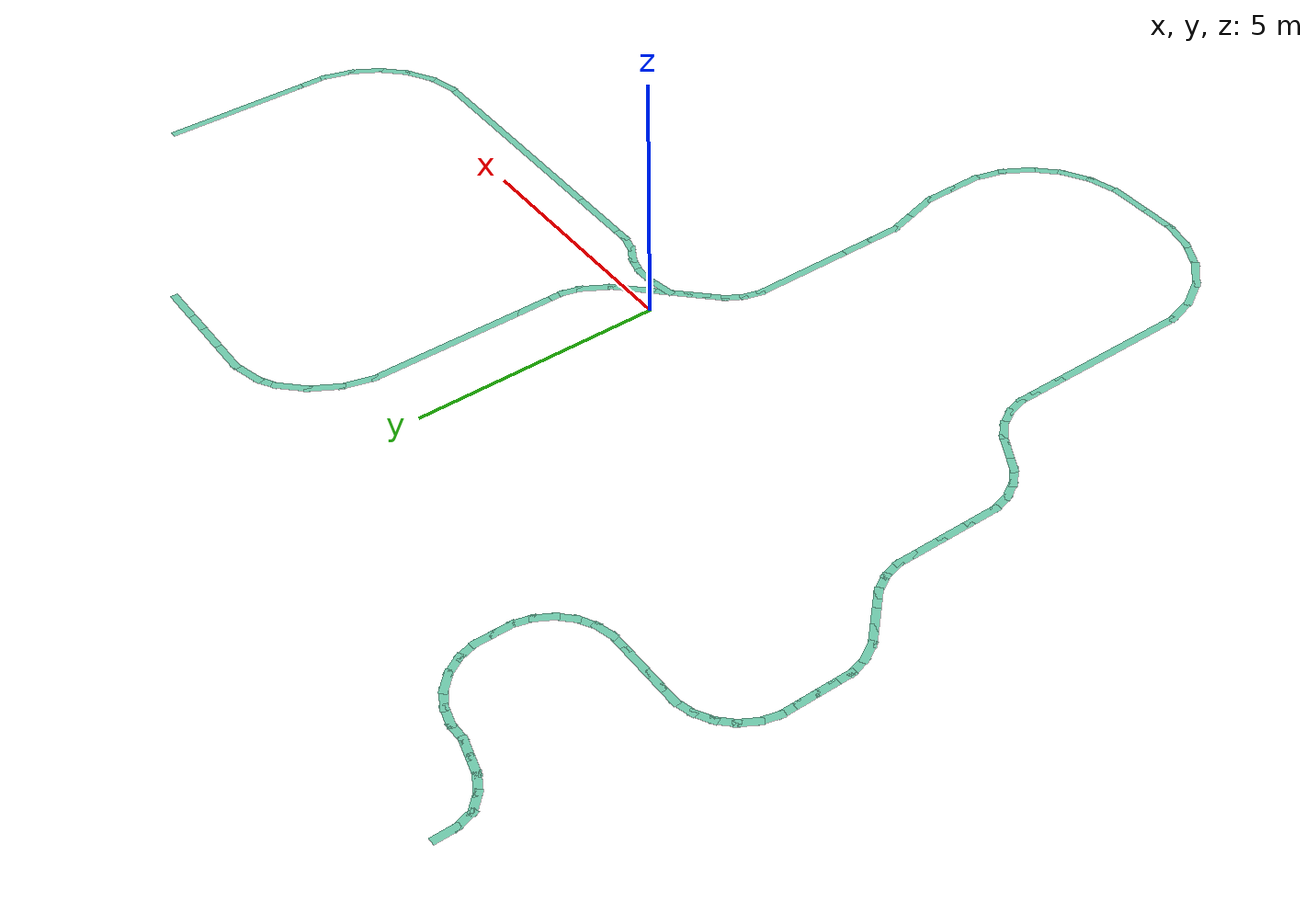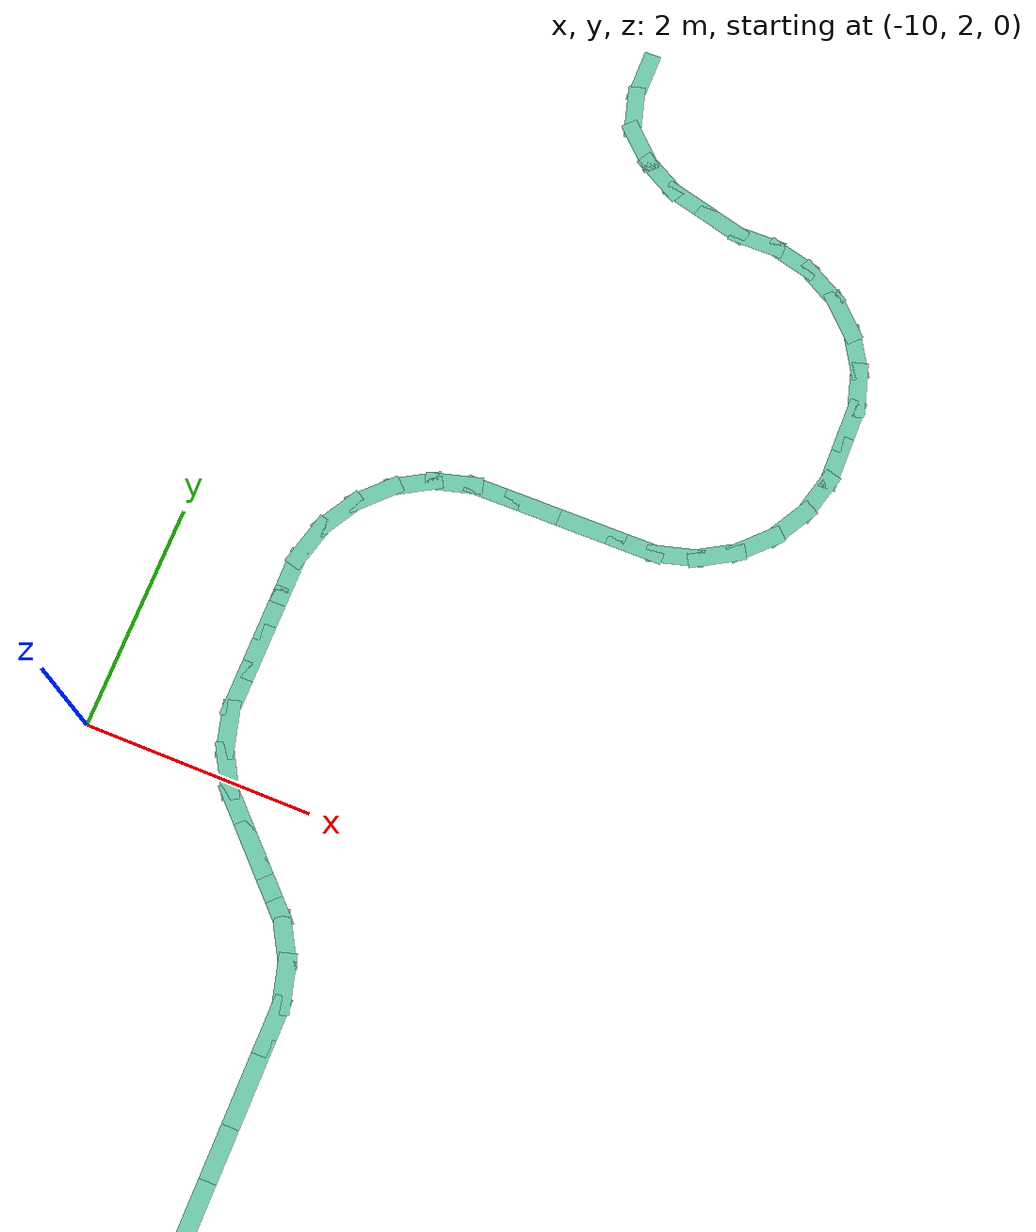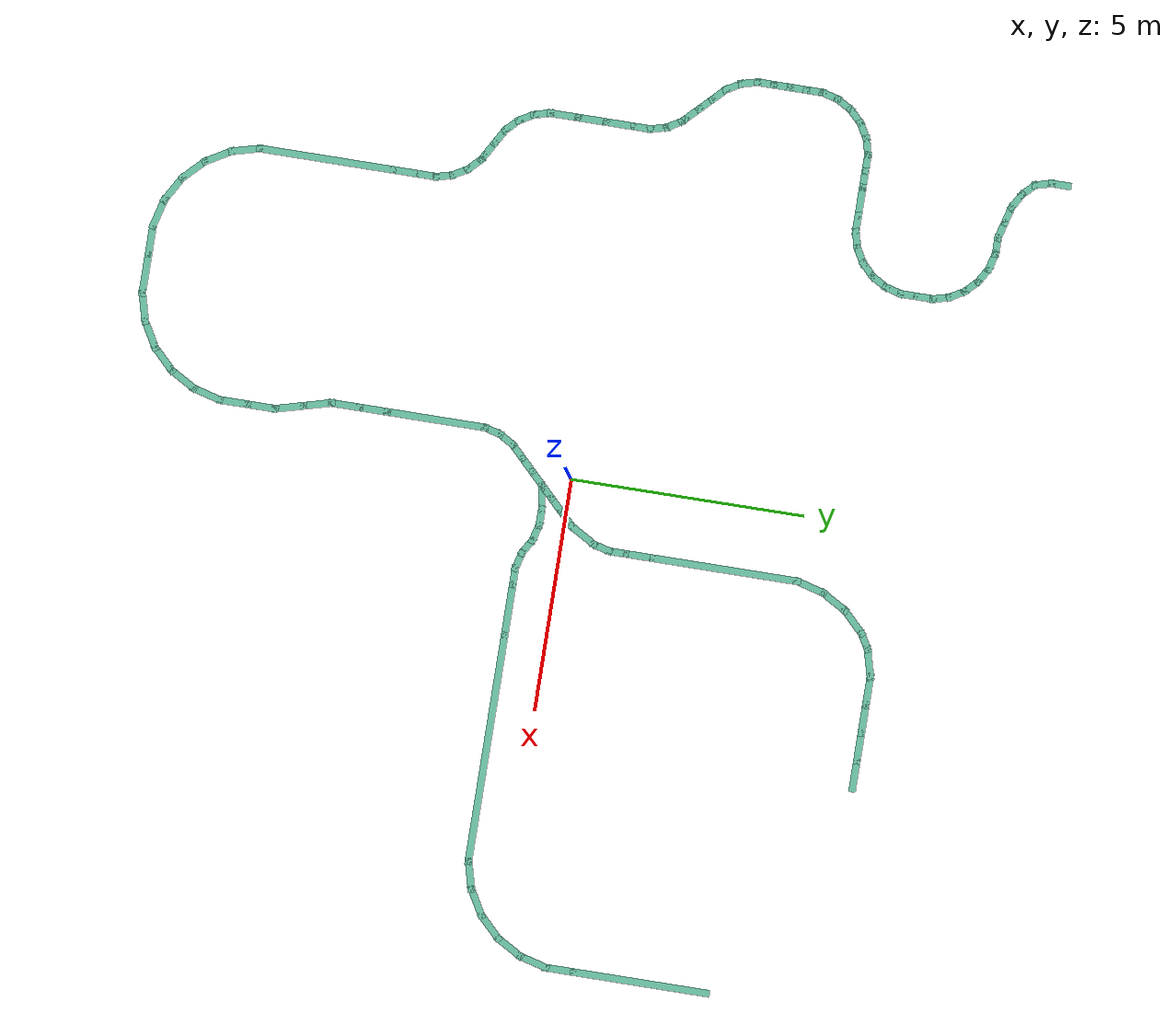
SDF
<?xml version='1.0'?>
<sdf version='1.6'>
  <model name='pomdp_path'>
    <pose frame=''>0.697999 -0.110454 0 0 -0 0</pose>
    <link name='Wall_100'>
      <collision name='Wall_100_Collision'>
        <geometry>
          <box>
            <size>0.5 0.15 0 </size>
          </box>
        </geometry>
        <pose frame=''>0 0 0.0001 0 -0 0</pose>
      </collision>
      <visual name='Wall_100_Visual'>
        <pose frame=''>0 0 0.0001 0 -0 0</pose>
        <geometry>
          <box>
            <size>0.5 0.15 0 </size>
          </box>
        </geometry>
        <material>
          <script>
            <uri>file://media/materials/scripts/gazebo.material</uri>
            <name>Gazebo/Grey</name>
          </script>
          <ambient>0.435294 0.796078 0.67451 1</ambient>
        </material>
        <meta>
          <layer>0</layer>
        </meta>
      </visual>
      <pose frame=''>-8.01598 8.51342 0 0 -0 -0.523599</pose>
    </link>
    <link name='Wall_101'>
      <collision name='Wall_101_Collision'>
        <geometry>
          <box>
            <size>0.5 0.15 0 </size>
          </box>
        </geometry>
        <pose frame=''>0 0 0.0001 0 -0 0</pose>
      </collision>
      <visual name='Wall_101_Visual'>
        <pose frame=''>0 0 0.0001 0 -0 0</pose>
        <geometry>
          <box>
            <size>0.5 0.15 0 </size>
          </box>
        </geometry>
        <material>
          <script>
            <uri>file://media/materials/scripts/gazebo.material</uri>
            <name>Gazebo/Grey</name>
          </script>
          <ambient>0.435294 0.796078 0.67451 1</ambient>
        </material>
        <meta>
          <layer>0</layer>
        </meta>
      </visual>
      <pose frame=''>-7.69538 8.38063 0 0 -0 -0.261799</pose>
    </link>
    <link name='Wall_102'>
      <collision name='Wall_102_Collision'>
        <geometry>
          <box>
            <size>0.5 0.15 0 </size>
          </box>
        </geometry>
        <pose frame=''>0 0 0.0001 0 -0 0</pose>
      </collision>
      <visual name='Wall_102_Visual'>
        <pose frame=''>0 0 0.0001 0 -0 0</pose>
        <geometry>
          <box>
            <size>0.5 0.15 0 </size>
          </box>
        </geometry>
        <material>
          <script>
            <uri>file://media/materials/scripts/gazebo.material</uri>
            <name>Gazebo/Grey</name>
          </script>
          <ambient>0.435294 0.796078 0.67451 1</ambient>
        </material>
        <meta>
          <layer>0</layer>
        </meta>
      </visual>
      <pose frame=''>-7.35731 8.29004 0 0 -0 -0.261799</pose>
    </link>
    <link name='Wall_103'>
      <collision name='Wall_103_Collision'>
        <geometry>
          <box>
            <size>0.5 0.15 0 </size>
          </box>
        </geometry>
        <pose frame=''>0 0 0.0001 0 -0 0</pose>
      </collision>
      <visual name='Wall_103_Visual'>
        <pose frame=''>0 0 0.0001 0 -0 0</pose>
        <geometry>
          <box>
            <size>0.5 0.15 0 </size>
          </box>
        </geometry>
        <material>
          <script>
            <uri>file://media/materials/scripts/gazebo.material</uri>
            <name>Gazebo/Grey</name>
          </script>
          <ambient>0.435294 0.796078 0.67451 1</ambient>
        </material>
        <meta>
          <layer>0</layer>
        </meta>
      </visual>
      <pose frame=''>-7.01327 8.24475 0 0 -0 0</pose>
    </link>
    <link name='Wall_104'>
      <collision name='Wall_104_Collision'>
        <geometry>
          <box>
            <size>0.5 0.15 0 </size>
          </box>
        </geometry>
        <pose frame=''>0 0 0.0001 0 -0 0</pose>
      </collision>
      <visual name='Wall_104_Visual'>
        <pose frame=''>0 0 0.0001 0 -0 0</pose>
        <geometry>
          <box>
            <size>0.5 0.15 0 </size>
          </box>
        </geometry>
        <material>
          <script>
            <uri>file://media/materials/scripts/gazebo.material</uri>
            <name>Gazebo/Grey</name>
          </script>
          <ambient>0.435294 0.796078 0.67451 1</ambient>
        </material>
        <meta>
          <layer>0</layer>
        </meta>
      </visual>
      <pose frame=''>-6.66924 8.19946 0 0 -0 -0.261799</pose>
    </link>
    <link name='Wall_105'>
      <collision name='Wall_105_Collision'>
        <geometry>
          <box>
            <size>0.5 0.15 0 </size>
          </box>
        </geometry>
        <pose frame=''>0 0 0.0001 0 -0 0</pose>
      </collision>
      <visual name='Wall_105_Visual'>
        <pose frame=''>0 0 0.0001 0 -0 0</pose>
        <geometry>
          <box>
            <size>0.5 0.15 0 </size>
          </box>
        </geometry>
        <material>
          <script>
            <uri>file://media/materials/scripts/gazebo.material</uri>
            <name>Gazebo/Grey</name>
          </script>
          <ambient>0.435294 0.796078 0.67451 1</ambient>
        </material>
        <meta>
          <layer>0</layer>
        </meta>
      </visual>
      <pose frame=''>-6.34865 8.06666 0 0 -0 -0.523599</pose>
    </link>
    <link name='Wall_107'>
      <collision name='Wall_107_Collision'>
        <geometry>
          <box>
            <size>0.5 0.15 0 </size>
          </box>
        </geometry>
        <pose frame=''>0 0 0.0001 0 -0 0</pose>
      </collision>
      <visual name='Wall_107_Visual'>
        <pose frame=''>0 0 0.0001 0 -0 0</pose>
        <geometry>
          <box>
            <size>0.5 0.15 0 </size>
          </box>
        </geometry>
        <material>
          <script>
            <uri>file://media/materials/scripts/gazebo.material</uri>
            <name>Gazebo/Grey</name>
          </script>
          <ambient>0.435294 0.796078 0.67451 1</ambient>
        </material>
        <meta>
          <layer>0</layer>
        </meta>
      </visual>
      <pose frame=''>-6.07335 7.85542 0 0 -0 -0.785398</pose>
    </link>
    <link name='Wall_108'>
      <collision name='Wall_108_Collision'>
        <geometry>
          <box>
            <size>0.5 0.15 0 </size>
          </box>
        </geometry>
        <pose frame=''>0 0 0.0001 0 -0 0</pose>
      </collision>
      <visual name='Wall_108_Visual'>
        <pose frame=''>0 0 0.0001 0 -0 0</pose>
        <geometry>
          <box>
            <size>0.5 0.15 0 </size>
          </box>
        </geometry>
        <material>
          <script>
            <uri>file://media/materials/scripts/gazebo.material</uri>
            <name>Gazebo/Grey</name>
          </script>
          <ambient>0.435294 0.796078 0.67451 1</ambient>
        </material>
        <meta>
          <layer>0</layer>
        </meta>
      </visual>
      <pose frame=''>-5.8621 7.58012 0 0 -0 -1.0472</pose>
    </link>
    <link name='Wall_109'>
      <collision name='Wall_109_Collision'>
        <geometry>
          <box>
            <size>0.5 0.15 0 </size>
          </box>
        </geometry>
        <pose frame=''>0 0 0.0001 0 -0 0</pose>
      </collision>
      <visual name='Wall_109_Visual'>
        <pose frame=''>0 0 0.0001 0 -0 0</pose>
        <geometry>
          <box>
            <size>0.5 0.15 0 </size>
          </box>
        </geometry>
        <material>
          <script>
            <uri>file://media/materials/scripts/gazebo.material</uri>
            <name>Gazebo/Grey</name>
          </script>
          <ambient>0.435294 0.796078 0.67451 1</ambient>
        </material>
        <meta>
          <layer>0</layer>
        </meta>
      </visual>
      <pose frame=''>-5.72931 7.25953 0 0 -0 -1.309</pose>
    </link>
    <link name='Wall_110'>
      <collision name='Wall_110_Collision'>
        <geometry>
          <box>
            <size>0.5 0.15 0 </size>
          </box>
        </geometry>
        <pose frame=''>0 0 0.0001 0 -0 0</pose>
      </collision>
      <visual name='Wall_110_Visual'>
        <pose frame=''>0 0 0.0001 0 -0 0</pose>
        <geometry>
          <box>
            <size>0.5 0.15 0 </size>
          </box>
        </geometry>
        <material>
          <script>
            <uri>file://media/materials/scripts/gazebo.material</uri>
            <name>Gazebo/Grey</name>
          </script>
          <ambient>0.435294 0.796078 0.67451 1</ambient>
        </material>
        <meta>
          <layer>0</layer>
        </meta>
      </visual>
      <pose frame=''>-5.68402 6.91549 0 0 -0 -1.5708</pose>
    </link>
    <link name='Wall_112'>
      <collision name='Wall_112_Collision'>
        <geometry>
          <box>
            <size>0.5 0.15 0 </size>
          </box>
        </geometry>
        <pose frame=''>0 0 0.0001 0 -0 0</pose>
      </collision>
      <visual name='Wall_112_Visual'>
        <pose frame=''>0 0 0.0001 0 -0 0</pose>
        <geometry>
          <box>
            <size>0.5 0.15 0 </size>
          </box>
        </geometry>
        <material>
          <script>
            <uri>file://media/materials/scripts/gazebo.material</uri>
            <name>Gazebo/Grey</name>
          </script>
          <ambient>0.435294 0.796078 0.67451 1</ambient>
        </material>
        <meta>
          <layer>0</layer>
        </meta>
      </visual>
      <pose frame=''>-5.68402 6.56549 0 0 -0 -1.5708</pose>
    </link>
    <link name='Wall_113'>
      <collision name='Wall_113_Collision'>
        <geometry>
          <box>
            <size>0.5 0.15 0 </size>
          </box>
        </geometry>
        <pose frame=''>0 0 0.0001 0 -0 0</pose>
      </collision>
      <visual name='Wall_113_Visual'>
        <pose frame=''>0 0 0.0001 0 -0 0</pose>
        <geometry>
          <box>
            <size>0.5 0.15 0 </size>
          </box>
        </geometry>
        <material>
          <script>
            <uri>file://media/materials/scripts/gazebo.material</uri>
            <name>Gazebo/Grey</name>
          </script>
          <ambient>0.435294 0.796078 0.67451 1</ambient>
        </material>
        <meta>
          <layer>0</layer>
        </meta>
      </visual>
      <pose frame=''>-5.72931 6.22145 0 0 -0 -1.8326</pose>
    </link>
    <link name='Wall_114'>
      <collision name='Wall_114_Collision'>
        <geometry>
          <box>
            <size>0.5 0.15 0 </size>
          </box>
        </geometry>
        <pose frame=''>0 0 0.0001 0 -0 0</pose>
      </collision>
      <visual name='Wall_114_Visual'>
        <pose frame=''>0 0 0.0001 0 -0 0</pose>
        <geometry>
          <box>
            <size>0.5 0.15 0 </size>
          </box>
        </geometry>
        <material>
          <script>
            <uri>file://media/materials/scripts/gazebo.material</uri>
            <name>Gazebo/Grey</name>
          </script>
          <ambient>0.435294 0.796078 0.67451 1</ambient>
        </material>
        <meta>
          <layer>0</layer>
        </meta>
      </visual>
      <pose frame=''>-5.8621 5.90086 0 0 -0 -2.0944</pose>
    </link>
    <link name='Wall_115'>
      <collision name='Wall_115_Collision'>
        <geometry>
          <box>
            <size>0.5 0.15 0 </size>
          </box>
        </geometry>
        <pose frame=''>0 0 0.0001 0 -0 0</pose>
      </collision>
      <visual name='Wall_115_Visual'>
        <pose frame=''>0 0 0.0001 0 -0 0</pose>
        <geometry>
          <box>
            <size>0.5 0.15 0 </size>
          </box>
        </geometry>
        <material>
          <script>
            <uri>file://media/materials/scripts/gazebo.material</uri>
            <name>Gazebo/Grey</name>
          </script>
          <ambient>0.435294 0.796078 0.67451 1</ambient>
        </material>
        <meta>
          <layer>0</layer>
        </meta>
      </visual>
      <pose frame=''>-6.07335 5.62556 0 0 -0 -2.35619</pose>
    </link>
    <link name='Wall_116'>
      <collision name='Wall_116_Collision'>
        <geometry>
          <box>
            <size>0.5 0.15 0 </size>
          </box>
        </geometry>
        <pose frame=''>0 0 0.0001 0 -0 0</pose>
      </collision>
      <visual name='Wall_116_Visual'>
        <pose frame=''>0 0 0.0001 0 -0 0</pose>
        <geometry>
          <box>
            <size>0.5 0.15 0 </size>
          </box>
        </geometry>
        <material>
          <script>
            <uri>file://media/materials/scripts/gazebo.material</uri>
            <name>Gazebo/Grey</name>
          </script>
          <ambient>0.435294 0.796078 0.67451 1</ambient>
        </material>
        <meta>
          <layer>0</layer>
        </meta>
      </visual>
      <pose frame=''>-6.34865 5.41432 0 0 -0 -2.61799</pose>
    </link>
    <link name='Wall_117'>
      <collision name='Wall_117_Collision'>
        <geometry>
          <box>
            <size>0.5 0.15 0 </size>
          </box>
        </geometry>
        <pose frame=''>0 0 0.0001 0 -0 0</pose>
      </collision>
      <visual name='Wall_117_Visual'>
        <pose frame=''>0 0 0.0001 0 -0 0</pose>
        <geometry>
          <box>
            <size>0.5 0.15 0 </size>
          </box>
        </geometry>
        <material>
          <script>
            <uri>file://media/materials/scripts/gazebo.material</uri>
            <name>Gazebo/Grey</name>
          </script>
          <ambient>0.435294 0.796078 0.67451 1</ambient>
        </material>
        <meta>
          <layer>0</layer>
        </meta>
      </visual>
      <pose frame=''>-6.66924 5.28153 0 0 -0 -2.87979</pose>
    </link>
    <link name='Wall_118'>
      <collision name='Wall_118_Collision'>
        <geometry>
          <box>
            <size>0.5 0.15 0 </size>
          </box>
        </geometry>
        <pose frame=''>0 0 0.0001 0 -0 0</pose>
      </collision>
      <visual name='Wall_118_Visual'>
        <pose frame=''>0 0 0.0001 0 -0 0</pose>
        <geometry>
          <box>
            <size>0.5 0.15 0 </size>
          </box>
        </geometry>
        <material>
          <script>
            <uri>file://media/materials/scripts/gazebo.material</uri>
            <name>Gazebo/Grey</name>
          </script>
          <ambient>0.435294 0.796078 0.67451 1</ambient>
        </material>
        <meta>
          <layer>0</layer>
        </meta>
      </visual>
      <pose frame=''>-7.01327 5.23623 0 0 -0 3.14159</pose>
    </link>
    <link name='Wall_119'>
      <collision name='Wall_119_Collision'>
        <geometry>
          <box>
            <size>0.75 0.15 0 </size>
          </box>
        </geometry>
        <pose frame=''>0 0 0.0001 0 -0 0</pose>
      </collision>
      <visual name='Wall_119_Visual'>
        <pose frame=''>0 0 0.0001 0 -0 0</pose>
        <geometry>
          <box>
            <size>0.75 0.15 0 </size>
          </box>
        </geometry>
        <material>
          <script>
            <uri>file://media/materials/scripts/gazebo.material</uri>
            <name>Gazebo/Grey</name>
          </script>
          <ambient>0.435294 0.796078 0.67451 1</ambient>
        </material>
        <meta>
          <layer>0</layer>
        </meta>
      </visual>
      <pose frame=''>-7.48827 5.23623 0 0 -0 3.14159</pose>
    </link>
    <link name='Wall_120'>
      <collision name='Wall_120_Collision'>
        <geometry>
          <box>
            <size>0.5 0.15 0 </size>
          </box>
        </geometry>
        <pose frame=''>0 0 0.0001 0 -0 0</pose>
      </collision>
      <visual name='Wall_120_Visual'>
        <pose frame=''>0 0 0.0001 0 -0 0</pose>
        <geometry>
          <box>
            <size>0.5 0.15 0 </size>
          </box>
        </geometry>
        <material>
          <script>
            <uri>file://media/materials/scripts/gazebo.material</uri>
            <name>Gazebo/Grey</name>
          </script>
          <ambient>0.435294 0.796078 0.67451 1</ambient>
        </material>
        <meta>
          <layer>0</layer>
        </meta>
      </visual>
      <pose frame=''>-7.96327 5.23623 0 0 -0 3.14159</pose>
    </link>
    <link name='Wall_121'>
      <collision name='Wall_121_Collision'>
        <geometry>
          <box>
            <size>0.5 0.15 0 </size>
          </box>
        </geometry>
        <pose frame=''>0 0 0.0001 0 -0 0</pose>
      </collision>
      <visual name='Wall_121_Visual'>
        <pose frame=''>0 0 0.0001 0 -0 0</pose>
        <geometry>
          <box>
            <size>0.5 0.15 0 </size>
          </box>
        </geometry>
        <material>
          <script>
            <uri>file://media/materials/scripts/gazebo.material</uri>
            <name>Gazebo/Grey</name>
          </script>
          <ambient>0.435294 0.796078 0.67451 1</ambient>
        </material>
        <meta>
          <layer>0</layer>
        </meta>
      </visual>
      <pose frame=''>-8.31327 5.23623 0 0 -0 3.14159</pose>
    </link>
    <link name='Wall_124'>
      <collision name='Wall_124_Collision'>
        <geometry>
          <box>
            <size>0.5 0.15 0 </size>
          </box>
        </geometry>
        <pose frame=''>0 0 0.0001 0 -0 0</pose>
      </collision>
      <visual name='Wall_124_Visual'>
        <pose frame=''>0 0 0.0001 0 -0 0</pose>
        <geometry>
          <box>
            <size>0.5 0.15 0 </size>
          </box>
        </geometry>
        <material>
          <script>
            <uri>file://media/materials/scripts/gazebo.material</uri>
            <name>Gazebo/Grey</name>
          </script>
          <ambient>0.435294 0.796078 0.67451 1</ambient>
        </material>
        <meta>
          <layer>0</layer>
        </meta>
      </visual>
      <pose frame=''>-8.65731 5.19094 0 0 -0 -2.87979</pose>
    </link>
    <link name='Wall_125'>
      <collision name='Wall_125_Collision'>
        <geometry>
          <box>
            <size>0.5 0.15 0 </size>
          </box>
        </geometry>
        <pose frame=''>0 0 0.0001 0 -0 0</pose>
      </collision>
      <visual name='Wall_125_Visual'>
        <pose frame=''>0 0 0.0001 0 -0 0</pose>
        <geometry>
          <box>
            <size>0.5 0.15 0 </size>
          </box>
        </geometry>
        <material>
          <script>
            <uri>file://media/materials/scripts/gazebo.material</uri>
            <name>Gazebo/Grey</name>
          </script>
          <ambient>0.435294 0.796078 0.67451 1</ambient>
        </material>
        <meta>
          <layer>0</layer>
        </meta>
      </visual>
      <pose frame=''>-8.9779 5.05815 0 0 -0 -2.61799</pose>
    </link>
    <link name='Wall_126'>
      <collision name='Wall_126_Collision'>
        <geometry>
          <box>
            <size>0.5 0.15 0 </size>
          </box>
        </geometry>
        <pose frame=''>0 0 0.0001 0 -0 0</pose>
      </collision>
      <visual name='Wall_126_Visual'>
        <pose frame=''>0 0 0.0001 0 -0 0</pose>
        <geometry>
          <box>
            <size>0.5 0.15 0 </size>
          </box>
        </geometry>
        <material>
          <script>
            <uri>file://media/materials/scripts/gazebo.material</uri>
            <name>Gazebo/Grey</name>
          </script>
          <ambient>0.435294 0.796078 0.67451 1</ambient>
        </material>
        <meta>
          <layer>0</layer>
        </meta>
      </visual>
      <pose frame=''>-9.2532 4.8469 0 0 -0 -2.35619</pose>
    </link>
    <link name='Wall_127'>
      <collision name='Wall_127_Collision'>
        <geometry>
          <box>
            <size>0.5 0.15 0 </size>
          </box>
        </geometry>
        <pose frame=''>0 0 0.0001 0 -0 0</pose>
      </collision>
      <visual name='Wall_127_Visual'>
        <pose frame=''>0 0 0.0001 0 -0 0</pose>
        <geometry>
          <box>
            <size>0.5 0.15 0 </size>
          </box>
        </geometry>
        <material>
          <script>
            <uri>file://media/materials/scripts/gazebo.material</uri>
            <name>Gazebo/Grey</name>
          </script>
          <ambient>0.435294 0.796078 0.67451 1</ambient>
        </material>
        <meta>
          <layer>0</layer>
        </meta>
      </visual>
      <pose frame=''>-9.46444 4.57161 0 0 -0 -2.0944</pose>
    </link>
    <link name='Wall_128'>
      <collision name='Wall_128_Collision'>
        <geometry>
          <box>
            <size>0.5 0.15 0 </size>
          </box>
        </geometry>
        <pose frame=''>0 0 0.0001 0 -0 0</pose>
      </collision>
      <visual name='Wall_128_Visual'>
        <pose frame=''>0 0 0.0001 0 -0 0</pose>
        <geometry>
          <box>
            <size>0.5 0.15 0 </size>
          </box>
        </geometry>
        <material>
          <script>
            <uri>file://media/materials/scripts/gazebo.material</uri>
            <name>Gazebo/Grey</name>
          </script>
          <ambient>0.435294 0.796078 0.67451 1</ambient>
        </material>
        <meta>
          <layer>0</layer>
        </meta>
      </visual>
      <pose frame=''>-9.59724 4.25101 0 0 -0 -1.8326</pose>
    </link>
    <link name='Wall_129'>
      <collision name='Wall_129_Collision'>
        <geometry>
          <box>
            <size>0.5 0.15 0 </size>
          </box>
        </geometry>
        <pose frame=''>0 0 0.0001 0 -0 0</pose>
      </collision>
      <visual name='Wall_129_Visual'>
        <pose frame=''>0 0 0.0001 0 -0 0</pose>
        <geometry>
          <box>
            <size>0.5 0.15 0 </size>
          </box>
        </geometry>
        <material>
          <script>
            <uri>file://media/materials/scripts/gazebo.material</uri>
            <name>Gazebo/Grey</name>
          </script>
          <ambient>0.435294 0.796078 0.67451 1</ambient>
        </material>
        <meta>
          <layer>0</layer>
        </meta>
      </visual>
      <pose frame=''>-9.64253 3.90698 0 0 -0 -1.5708</pose>
    </link>
    <link name='Wall_130'>
      <collision name='Wall_130_Collision'>
        <geometry>
          <box>
            <size>0.5 0.15 0 </size>
          </box>
        </geometry>
        <pose frame=''>0 0 0.0001 0 -0 0</pose>
      </collision>
      <visual name='Wall_130_Visual'>
        <pose frame=''>0 0 0.0001 0 -0 0</pose>
        <geometry>
          <box>
            <size>0.5 0.15 0 </size>
          </box>
        </geometry>
        <material>
          <script>
            <uri>file://media/materials/scripts/gazebo.material</uri>
            <name>Gazebo/Grey</name>
          </script>
          <ambient>0.435294 0.796078 0.67451 1</ambient>
        </material>
        <meta>
          <layer>0</layer>
        </meta>
      </visual>
      <pose frame=''>-9.64253 3.55698 0 0 -0 -1.5708</pose>
    </link>
    <link name='Wall_131'>
      <collision name='Wall_131_Collision'>
        <geometry>
          <box>
            <size>0.5 0.15 0 </size>
          </box>
        </geometry>
        <pose frame=''>0 0 0.0001 0 -0 0</pose>
      </collision>
      <visual name='Wall_131_Visual'>
        <pose frame=''>0 0 0.0001 0 -0 0</pose>
        <geometry>
          <box>
            <size>0.5 0.15 0 </size>
          </box>
        </geometry>
        <material>
          <script>
            <uri>file://media/materials/scripts/gazebo.material</uri>
            <name>Gazebo/Grey</name>
          </script>
          <ambient>0.435294 0.796078 0.67451 1</ambient>
        </material>
        <meta>
          <layer>0</layer>
        </meta>
      </visual>
      <pose frame=''>-9.64253 3.20698 0 0 -0 -1.5708</pose>
    </link>
    <link name='Wall_133'>
      <collision name='Wall_133_Collision'>
        <geometry>
          <box>
            <size>0.5 0.15 0 </size>
          </box>
        </geometry>
        <pose frame=''>0 0 0.0001 0 -0 0</pose>
      </collision>
      <visual name='Wall_133_Visual'>
        <pose frame=''>0 0 0.0001 0 -0 0</pose>
        <geometry>
          <box>
            <size>0.5 0.15 0 </size>
          </box>
        </geometry>
        <material>
          <script>
            <uri>file://media/materials/scripts/gazebo.material</uri>
            <name>Gazebo/Grey</name>
          </script>
          <ambient>0.435294 0.796078 0.67451 1</ambient>
        </material>
        <meta>
          <layer>0</layer>
        </meta>
      </visual>
      <pose frame=''>-9.64253 2.85698 0 0 -0 -1.5708</pose>
    </link>
    <link name='Wall_134'>
      <collision name='Wall_134_Collision'>
        <geometry>
          <box>
            <size>0.5 0.15 0 </size>
          </box>
        </geometry>
        <pose frame=''>0 0 0.0001 0 -0 0</pose>
      </collision>
      <visual name='Wall_134_Visual'>
        <pose frame=''>0 0 0.0001 0 -0 0</pose>
        <geometry>
          <box>
            <size>0.5 0.15 0 </size>
          </box>
        </geometry>
        <material>
          <script>
            <uri>file://media/materials/scripts/gazebo.material</uri>
            <name>Gazebo/Grey</name>
          </script>
          <ambient>0.435294 0.796078 0.67451 1</ambient>
        </material>
        <meta>
          <layer>0</layer>
        </meta>
      </visual>
      <pose frame=''>-9.59724 2.51294 0 0 -0 -1.309</pose>
    </link>
    <link name='Wall_135'>
      <collision name='Wall_135_Collision'>
        <geometry>
          <box>
            <size>0.5 0.15 0 </size>
          </box>
        </geometry>
        <pose frame=''>0 0 0.0001 0 -0 0</pose>
      </collision>
      <visual name='Wall_135_Visual'>
        <pose frame=''>0 0 0.0001 0 -0 0</pose>
        <geometry>
          <box>
            <size>0.5 0.15 0 </size>
          </box>
        </geometry>
        <material>
          <script>
            <uri>file://media/materials/scripts/gazebo.material</uri>
            <name>Gazebo/Grey</name>
          </script>
          <ambient>0.435294 0.796078 0.67451 1</ambient>
        </material>
        <meta>
          <layer>0</layer>
        </meta>
      </visual>
      <pose frame=''>-9.46444 2.19235 0 0 -0 -1.0472</pose>
    </link>
    <link name='Wall_136'>
      <collision name='Wall_136_Collision'>
        <geometry>
          <box>
            <size>0.5 0.15 0 </size>
          </box>
        </geometry>
        <pose frame=''>0 0 0.0001 0 -0 0</pose>
      </collision>
      <visual name='Wall_136_Visual'>
        <pose frame=''>0 0 0.0001 0 -0 0</pose>
        <geometry>
          <box>
            <size>0.5 0.15 0 </size>
          </box>
        </geometry>
        <material>
          <script>
            <uri>file://media/materials/scripts/gazebo.material</uri>
            <name>Gazebo/Grey</name>
          </script>
          <ambient>0.435294 0.796078 0.67451 1</ambient>
        </material>
        <meta>
          <layer>0</layer>
        </meta>
      </visual>
      <pose frame=''>-9.2532 1.91705 0 0 -0 -0.785398</pose>
    </link>
    <link name='Wall_137'>
      <collision name='Wall_137_Collision'>
        <geometry>
          <box>
            <size>0.5 0.15 0 </size>
          </box>
        </geometry>
        <pose frame=''>0 0 0.0001 0 -0 0</pose>
      </collision>
      <visual name='Wall_137_Visual'>
        <pose frame=''>0 0 0.0001 0 -0 0</pose>
        <geometry>
          <box>
            <size>0.5 0.15 0 </size>
          </box>
        </geometry>
        <material>
          <script>
            <uri>file://media/materials/scripts/gazebo.material</uri>
            <name>Gazebo/Grey</name>
          </script>
          <ambient>0.435294 0.796078 0.67451 1</ambient>
        </material>
        <meta>
          <layer>0</layer>
        </meta>
      </visual>
      <pose frame=''>-9.00571 1.66956 0 0 -0 -0.785398</pose>
    </link>
    <link name='Wall_138'>
      <collision name='Wall_138_Collision'>
        <geometry>
          <box>
            <size>0.5 0.15 0 </size>
          </box>
        </geometry>
        <pose frame=''>0 0 0.0001 0 -0 0</pose>
      </collision>
      <visual name='Wall_138_Visual'>
        <pose frame=''>0 0 0.0001 0 -0 0</pose>
        <geometry>
          <box>
            <size>0.5 0.15 0 </size>
          </box>
        </geometry>
        <material>
          <script>
            <uri>file://media/materials/scripts/gazebo.material</uri>
            <name>Gazebo/Grey</name>
          </script>
          <ambient>0.435294 0.796078 0.67451 1</ambient>
        </material>
        <meta>
          <layer>0</layer>
        </meta>
      </visual>
      <pose frame=''>-8.75822 1.42208 0 0 -0 -0.785398</pose>
    </link>
    <link name='Wall_148'>
      <collision name='Wall_148_Collision'>
        <geometry>
          <box>
            <size>0.25 0.15 0 </size>
          </box>
        </geometry>
        <pose frame=''>0 0 0.0001 0 -0 0</pose>
      </collision>
      <visual name='Wall_148_Visual'>
        <pose frame=''>0 0 0.0001 0 -0 0</pose>
        <geometry>
          <box>
            <size>0.25 0.15 0 </size>
          </box>
        </geometry>
        <material>
          <script>
            <uri>file://media/materials/scripts/gazebo.material</uri>
            <name>Gazebo/Grey</name>
          </script>
          <ambient>0.435294 0.796078 0.67451 1</ambient>
        </material>
        <meta>
          <layer>0</layer>
        </meta>
      </visual>
      <pose frame=''>-8.59913 1.26298 0 0 -0 -0.785398</pose>
    </link>
    <link name='Wall_149'>
      <collision name='Wall_149_Collision'>
        <geometry>
          <box>
            <size>0.5 0.15 0 </size>
          </box>
        </geometry>
        <pose frame=''>0 0 0.0001 0 -0 0</pose>
      </collision>
      <visual name='Wall_149_Visual'>
        <pose frame=''>0 0 0.0001 0 -0 0</pose>
        <geometry>
          <box>
            <size>0.5 0.15 0 </size>
          </box>
        </geometry>
        <material>
          <script>
            <uri>file://media/materials/scripts/gazebo.material</uri>
            <name>Gazebo/Grey</name>
          </script>
          <ambient>0.435294 0.796078 0.67451 1</ambient>
        </material>
        <meta>
          <layer>0</layer>
        </meta>
      </visual>
      <pose frame=''>-8.47627 1.07607 0 0 -0 -1.0472</pose>
    </link>
    <link name='Wall_150'>
      <collision name='Wall_150_Collision'>
        <geometry>
          <box>
            <size>0.5 0.15 0 </size>
          </box>
        </geometry>
        <pose frame=''>0 0 0.0001 0 -0 0</pose>
      </collision>
      <visual name='Wall_150_Visual'>
        <pose frame=''>0 0 0.0001 0 -0 0</pose>
        <geometry>
          <box>
            <size>0.5 0.15 0 </size>
          </box>
        </geometry>
        <material>
          <script>
            <uri>file://media/materials/scripts/gazebo.material</uri>
            <name>Gazebo/Grey</name>
          </script>
          <ambient>0.435294 0.796078 0.67451 1</ambient>
        </material>
        <meta>
          <layer>0</layer>
        </meta>
      </visual>
      <pose frame=''>-8.34348 0.755476 0 0 -0 -1.309</pose>
    </link>
    <link name='Wall_151'>
      <collision name='Wall_151_Collision'>
        <geometry>
          <box>
            <size>0.5 0.15 0 </size>
          </box>
        </geometry>
        <pose frame=''>0 0 0.0001 0 -0 0</pose>
      </collision>
      <visual name='Wall_151_Visual'>
        <pose frame=''>0 0 0.0001 0 -0 0</pose>
        <geometry>
          <box>
            <size>0.5 0.15 0 </size>
          </box>
        </geometry>
        <material>
          <script>
            <uri>file://media/materials/scripts/gazebo.material</uri>
            <name>Gazebo/Grey</name>
          </script>
          <ambient>0.435294 0.796078 0.67451 1</ambient>
        </material>
        <meta>
          <layer>0</layer>
        </meta>
      </visual>
      <pose frame=''>-8.29818 0.411439 0 0 -0 -1.5708</pose>
    </link>
    <link name='Wall_153'>
      <collision name='Wall_153_Collision'>
        <geometry>
          <box>
            <size>0.75 0.15 0 </size>
          </box>
        </geometry>
        <pose frame=''>0 0 0.0001 0 -0 0</pose>
      </collision>
      <visual name='Wall_153_Visual'>
        <pose frame=''>0 0 0.0001 0 -0 0</pose>
        <geometry>
          <box>
            <size>0.75 0.15 0 </size>
          </box>
        </geometry>
        <material>
          <script>
            <uri>file://media/materials/scripts/gazebo.material</uri>
            <name>Gazebo/Grey</name>
          </script>
          <ambient>0.435294 0.796078 0.67451 1</ambient>
        </material>
        <meta>
          <layer>0</layer>
        </meta>
      </visual>
      <pose frame=''>-8.29818 -0.063561 0 0 -0 -1.5708</pose>
    </link>
    <link name='Wall_154'>
      <collision name='Wall_154_Collision'>
        <geometry>
          <box>
            <size>0.75 0.15 0 </size>
          </box>
        </geometry>
        <pose frame=''>0 0 0.0001 0 -0 0</pose>
      </collision>
      <visual name='Wall_154_Visual'>
        <pose frame=''>0 0 0.0001 0 -0 0</pose>
        <geometry>
          <box>
            <size>0.75 0.15 0 </size>
          </box>
        </geometry>
        <material>
          <script>
            <uri>file://media/materials/scripts/gazebo.material</uri>
            <name>Gazebo/Grey</name>
          </script>
          <ambient>0.435294 0.796078 0.67451 1</ambient>
        </material>
        <meta>
          <layer>0</layer>
        </meta>
      </visual>
      <pose frame=''>-8.29818 -0.663561 0 0 -0 -1.5708</pose>
    </link>
    <link name='Wall_156'>
      <collision name='Wall_156_Collision'>
        <geometry>
          <box>
            <size>0.75 0.15 0 </size>
          </box>
        </geometry>
        <pose frame=''>0 0 0.0001 0 -0 0</pose>
      </collision>
      <visual name='Wall_156_Visual'>
        <pose frame=''>0 0 0.0001 0 -0 0</pose>
        <geometry>
          <box>
            <size>0.75 0.15 0 </size>
          </box>
        </geometry>
        <material>
          <script>
            <uri>file://media/materials/scripts/gazebo.material</uri>
            <name>Gazebo/Grey</name>
          </script>
          <ambient>0.435294 0.796078 0.67451 1</ambient>
        </material>
        <meta>
          <layer>0</layer>
        </meta>
      </visual>
      <pose frame=''>-8.29818 -1.26356 0 0 -0 -1.5708</pose>
    </link>
    <link name='Wall_157'>
      <collision name='Wall_157_Collision'>
        <geometry>
          <box>
            <size>0.5 0.15 0 </size>
          </box>
        </geometry>
        <pose frame=''>0 0 0.0001 0 -0 0</pose>
      </collision>
      <visual name='Wall_157_Visual'>
        <pose frame=''>0 0 0.0001 0 -0 0</pose>
        <geometry>
          <box>
            <size>0.5 0.15 0 </size>
          </box>
        </geometry>
        <material>
          <script>
            <uri>file://media/materials/scripts/gazebo.material</uri>
            <name>Gazebo/Grey</name>
          </script>
          <ambient>0.435294 0.796078 0.67451 1</ambient>
        </material>
        <meta>
          <layer>0</layer>
        </meta>
      </visual>
      <pose frame=''>-8.25289 -1.7326 0 0 -0 -1.309</pose>
    </link>
    <link name='Wall_158'>
      <collision name='Wall_158_Collision'>
        <geometry>
          <box>
            <size>0.5 0.15 0 </size>
          </box>
        </geometry>
        <pose frame=''>0 0 0.0001 0 -0 0</pose>
      </collision>
      <visual name='Wall_158_Visual'>
        <pose frame=''>0 0 0.0001 0 -0 0</pose>
        <geometry>
          <box>
            <size>0.5 0.15 0 </size>
          </box>
        </geometry>
        <material>
          <script>
            <uri>file://media/materials/scripts/gazebo.material</uri>
            <name>Gazebo/Grey</name>
          </script>
          <ambient>0.435294 0.796078 0.67451 1</ambient>
        </material>
        <meta>
          <layer>0</layer>
        </meta>
      </visual>
      <pose frame=''>-8.1201 -2.05319 0 0 -0 -1.0472</pose>
    </link>
    <link name='Wall_159'>
      <collision name='Wall_159_Collision'>
        <geometry>
          <box>
            <size>0.5 0.15 0 </size>
          </box>
        </geometry>
        <pose frame=''>0 0 0.0001 0 -0 0</pose>
      </collision>
      <visual name='Wall_159_Visual'>
        <pose frame=''>0 0 0.0001 0 -0 0</pose>
        <geometry>
          <box>
            <size>0.5 0.15 0 </size>
          </box>
        </geometry>
        <material>
          <script>
            <uri>file://media/materials/scripts/gazebo.material</uri>
            <name>Gazebo/Grey</name>
          </script>
          <ambient>0.435294 0.796078 0.67451 1</ambient>
        </material>
        <meta>
          <layer>0</layer>
        </meta>
      </visual>
      <pose frame=''>-7.90885 -2.32849 0 0 -0 -0.785398</pose>
    </link>
    <link name='Wall_160'>
      <collision name='Wall_160_Collision'>
        <geometry>
          <box>
            <size>0.5 0.15 0 </size>
          </box>
        </geometry>
        <pose frame=''>0 0 0.0001 0 -0 0</pose>
      </collision>
      <visual name='Wall_160_Visual'>
        <pose frame=''>0 0 0.0001 0 -0 0</pose>
        <geometry>
          <box>
            <size>0.5 0.15 0 </size>
          </box>
        </geometry>
        <material>
          <script>
            <uri>file://media/materials/scripts/gazebo.material</uri>
            <name>Gazebo/Grey</name>
          </script>
          <ambient>0.435294 0.796078 0.67451 1</ambient>
        </material>
        <meta>
          <layer>0</layer>
        </meta>
      </visual>
      <pose frame=''>-7.63356 -2.53973 0 0 -0 -0.523599</pose>
    </link>
    <link name='Wall_161'>
      <collision name='Wall_161_Collision'>
        <geometry>
          <box>
            <size>0.5 0.15 0 </size>
          </box>
        </geometry>
        <pose frame=''>0 0 0.0001 0 -0 0</pose>
      </collision>
      <visual name='Wall_161_Visual'>
        <pose frame=''>0 0 0.0001 0 -0 0</pose>
        <geometry>
          <box>
            <size>0.5 0.15 0 </size>
          </box>
        </geometry>
        <material>
          <script>
            <uri>file://media/materials/scripts/gazebo.material</uri>
            <name>Gazebo/Grey</name>
          </script>
          <ambient>0.435294 0.796078 0.67451 1</ambient>
        </material>
        <meta>
          <layer>0</layer>
        </meta>
      </visual>
      <pose frame=''>-7.33045 -2.71473 0 0 -0 -0.523599</pose>
    </link>
    <link name='Wall_167'>
      <collision name='Wall_167_Collision'>
        <geometry>
          <box>
            <size>0.25 0.15 0 </size>
          </box>
        </geometry>
        <pose frame=''>0 0 0.0001 0 -0 0</pose>
      </collision>
      <visual name='Wall_167_Visual'>
        <pose frame=''>0 0 0.0001 0 -0 0</pose>
        <geometry>
          <box>
            <size>0.25 0.15 0 </size>
          </box>
        </geometry>
        <material>
          <script>
            <uri>file://media/materials/scripts/gazebo.material</uri>
            <name>Gazebo/Grey</name>
          </script>
          <ambient>0.435294 0.796078 0.67451 1</ambient>
        </material>
        <meta>
          <layer>0</layer>
        </meta>
      </visual>
      <pose frame=''>-7.13559 -2.82723 0 0 -0 -0.523599</pose>
    </link>
    <link name='Wall_168'>
      <collision name='Wall_168_Collision'>
        <geometry>
          <box>
            <size>0.5 0.15 0 </size>
          </box>
        </geometry>
        <pose frame=''>0 0 0.0001 0 -0 0</pose>
      </collision>
      <visual name='Wall_168_Visual'>
        <pose frame=''>0 0 0.0001 0 -0 0</pose>
        <geometry>
          <box>
            <size>0.5 0.15 0 </size>
          </box>
        </geometry>
        <material>
          <script>
            <uri>file://media/materials/scripts/gazebo.material</uri>
            <name>Gazebo/Grey</name>
          </script>
          <ambient>0.435294 0.796078 0.67451 1</ambient>
        </material>
        <meta>
          <layer>0</layer>
        </meta>
      </visual>
      <pose frame=''>-6.96855 -2.97598 0 0 -0 -0.785398</pose>
    </link>
    <link name='Wall_169'>
      <collision name='Wall_169_Collision'>
        <geometry>
          <box>
            <size>0.5 0.15 0 </size>
          </box>
        </geometry>
        <pose frame=''>0 0 0.0001 0 -0 0</pose>
      </collision>
      <visual name='Wall_169_Visual'>
        <pose frame=''>0 0 0.0001 0 -0 0</pose>
        <geometry>
          <box>
            <size>0.5 0.15 0 </size>
          </box>
        </geometry>
        <material>
          <script>
            <uri>file://media/materials/scripts/gazebo.material</uri>
            <name>Gazebo/Grey</name>
          </script>
          <ambient>0.435294 0.796078 0.67451 1</ambient>
        </material>
        <meta>
          <layer>0</layer>
        </meta>
      </visual>
      <pose frame=''>-6.7573 -3.25127 0 0 -0 -1.0472</pose>
    </link>
    <link name='Wall_170'>
      <collision name='Wall_170_Collision'>
        <geometry>
          <box>
            <size>0.5 0.15 0 </size>
          </box>
        </geometry>
        <pose frame=''>0 0 0.0001 0 -0 0</pose>
      </collision>
      <visual name='Wall_170_Visual'>
        <pose frame=''>0 0 0.0001 0 -0 0</pose>
        <geometry>
          <box>
            <size>0.5 0.15 0 </size>
          </box>
        </geometry>
        <material>
          <script>
            <uri>file://media/materials/scripts/gazebo.material</uri>
            <name>Gazebo/Grey</name>
          </script>
          <ambient>0.435294 0.796078 0.67451 1</ambient>
        </material>
        <meta>
          <layer>0</layer>
        </meta>
      </visual>
      <pose frame=''>-6.62451 -3.57186 0 0 -0 -1.309</pose>
    </link>
    <link name='Wall_171'>
      <collision name='Wall_171_Collision'>
        <geometry>
          <box>
            <size>0.5 0.15 0 </size>
          </box>
        </geometry>
        <pose frame=''>0 0 0.0001 0 -0 0</pose>
      </collision>
      <visual name='Wall_171_Visual'>
        <pose frame=''>0 0 0.0001 0 -0 0</pose>
        <geometry>
          <box>
            <size>0.5 0.15 0 </size>
          </box>
        </geometry>
        <material>
          <script>
            <uri>file://media/materials/scripts/gazebo.material</uri>
            <name>Gazebo/Grey</name>
          </script>
          <ambient>0.435294 0.796078 0.67451 1</ambient>
        </material>
        <meta>
          <layer>0</layer>
        </meta>
      </visual>
      <pose frame=''>-6.57922 -3.9159 0 0 -0 -1.5708</pose>
    </link>
    <link name='Wall_172'>
      <collision name='Wall_172_Collision'>
        <geometry>
          <box>
            <size>0.75 0.15 0 </size>
          </box>
        </geometry>
        <pose frame=''>0 0 0.0001 0 -0 0</pose>
      </collision>
      <visual name='Wall_172_Visual'>
        <pose frame=''>0 0 0.0001 0 -0 0</pose>
        <geometry>
          <box>
            <size>0.75 0.15 0 </size>
          </box>
        </geometry>
        <material>
          <script>
            <uri>file://media/materials/scripts/gazebo.material</uri>
            <name>Gazebo/Grey</name>
          </script>
          <ambient>0.435294 0.796078 0.67451 1</ambient>
        </material>
        <meta>
          <layer>0</layer>
        </meta>
      </visual>
      <pose frame=''>-6.57922 -4.3909 0 0 -0 -1.5708</pose>
    </link>
    <link name='Wall_176'>
      <collision name='Wall_176_Collision'>
        <geometry>
          <box>
            <size>3 0.15 0 </size>
          </box>
        </geometry>
        <pose frame=''>0 0 0.0001 0 -0 0</pose>
      </collision>
      <visual name='Wall_176_Visual'>
        <pose frame=''>0 0 0.0001 0 -0 0</pose>
        <geometry>
          <box>
            <size>3 0.15 0 </size>
          </box>
        </geometry>
        <material>
          <script>
            <uri>file://media/materials/scripts/gazebo.material</uri>
            <name>Gazebo/Grey</name>
          </script>
          <ambient>0.435294 0.796078 0.67451 1</ambient>
        </material>
        <meta>
          <layer>0</layer>
        </meta>
      </visual>
      <pose frame=''>-6.57922 -6.1159 0 0 -0 -1.5708</pose>
    </link>
    <link name='Wall_177'>
      <collision name='Wall_177_Collision'>
        <geometry>
          <box>
            <size>0.75 0.15 0 </size>
          </box>
        </geometry>
        <pose frame=''>0 0 0.0001 0 -0 0</pose>
      </collision>
      <visual name='Wall_177_Visual'>
        <pose frame=''>0 0 0.0001 0 -0 0</pose>
        <geometry>
          <box>
            <size>0.75 0.15 0 </size>
          </box>
        </geometry>
        <material>
          <script>
            <uri>file://media/materials/scripts/gazebo.material</uri>
            <name>Gazebo/Grey</name>
          </script>
          <ambient>0.435294 0.796078 0.67451 1</ambient>
        </material>
        <meta>
          <layer>0</layer>
        </meta>
      </visual>
      <pose frame=''>-6.50157 -7.83068 0 0 -0 -1.309</pose>
    </link>
    <link name='Wall_178'>
      <collision name='Wall_178_Collision'>
        <geometry>
          <box>
            <size>0.75 0.15 0 </size>
          </box>
        </geometry>
        <pose frame=''>0 0 0.0001 0 -0 0</pose>
      </collision>
      <visual name='Wall_178_Visual'>
        <pose frame=''>0 0 0.0001 0 -0 0</pose>
        <geometry>
          <box>
            <size>0.75 0.15 0 </size>
          </box>
        </geometry>
        <material>
          <script>
            <uri>file://media/materials/scripts/gazebo.material</uri>
            <name>Gazebo/Grey</name>
          </script>
          <ambient>0.435294 0.796078 0.67451 1</ambient>
        </material>
        <meta>
          <layer>0</layer>
        </meta>
      </visual>
      <pose frame=''>-6.27392 -8.38026 0 0 -0 -1.0472</pose>
    </link>
    <link name='Wall_179'>
      <collision name='Wall_179_Collision'>
        <geometry>
          <box>
            <size>0.75 0.15 0 </size>
          </box>
        </geometry>
        <pose frame=''>0 0 0.0001 0 -0 0</pose>
      </collision>
      <visual name='Wall_179_Visual'>
        <pose frame=''>0 0 0.0001 0 -0 0</pose>
        <geometry>
          <box>
            <size>0.75 0.15 0 </size>
          </box>
        </geometry>
        <material>
          <script>
            <uri>file://media/materials/scripts/gazebo.material</uri>
            <name>Gazebo/Grey</name>
          </script>
          <ambient>0.435294 0.796078 0.67451 1</ambient>
        </material>
        <meta>
          <layer>0</layer>
        </meta>
      </visual>
      <pose frame=''>-5.91179 -8.8522 0 0 -0 -0.785398</pose>
    </link>
    <link name='Wall_180'>
      <collision name='Wall_180_Collision'>
        <geometry>
          <box>
            <size>0.75 0.15 0 </size>
          </box>
        </geometry>
        <pose frame=''>0 0 0.0001 0 -0 0</pose>
      </collision>
      <visual name='Wall_180_Visual'>
        <pose frame=''>0 0 0.0001 0 -0 0</pose>
        <geometry>
          <box>
            <size>0.75 0.15 0 </size>
          </box>
        </geometry>
        <material>
          <script>
            <uri>file://media/materials/scripts/gazebo.material</uri>
            <name>Gazebo/Grey</name>
          </script>
          <ambient>0.435294 0.796078 0.67451 1</ambient>
        </material>
        <meta>
          <layer>0</layer>
        </meta>
      </visual>
      <pose frame=''>-5.43985 -9.21434 0 0 -0 -0.523599</pose>
    </link>
    <link name='Wall_181'>
      <collision name='Wall_181_Collision'>
        <geometry>
          <box>
            <size>0.75 0.15 0 </size>
          </box>
        </geometry>
        <pose frame=''>0 0 0.0001 0 -0 0</pose>
      </collision>
      <visual name='Wall_181_Visual'>
        <pose frame=''>0 0 0.0001 0 -0 0</pose>
        <geometry>
          <box>
            <size>0.75 0.15 0 </size>
          </box>
        </geometry>
        <material>
          <script>
            <uri>file://media/materials/scripts/gazebo.material</uri>
            <name>Gazebo/Grey</name>
          </script>
          <ambient>0.435294 0.796078 0.67451 1</ambient>
        </material>
        <meta>
          <layer>0</layer>
        </meta>
      </visual>
      <pose frame=''>-4.89027 -9.44198 0 0 -0 -0.261799</pose>
    </link>
    <link name='Wall_182'>
      <collision name='Wall_182_Collision'>
        <geometry>
          <box>
            <size>0.75 0.15 0 </size>
          </box>
        </geometry>
        <pose frame=''>0 0 0.0001 0 -0 0</pose>
      </collision>
      <visual name='Wall_182_Visual'>
        <pose frame=''>0 0 0.0001 0 -0 0</pose>
        <geometry>
          <box>
            <size>0.75 0.15 0 </size>
          </box>
        </geometry>
        <material>
          <script>
            <uri>file://media/materials/scripts/gazebo.material</uri>
            <name>Gazebo/Grey</name>
          </script>
          <ambient>0.435294 0.796078 0.67451 1</ambient>
        </material>
        <meta>
          <layer>0</layer>
        </meta>
      </visual>
      <pose frame=''>-4.30049 -9.51963 0 0 -0 0</pose>
    </link>
    <link name='Wall_183'>
      <collision name='Wall_183_Collision'>
        <geometry>
          <box>
            <size>1 0.15 0 </size>
          </box>
        </geometry>
        <pose frame=''>0 0 0.0001 0 -0 0</pose>
      </collision>
      <visual name='Wall_183_Visual'>
        <pose frame=''>0 0 0.0001 0 -0 0</pose>
        <geometry>
          <box>
            <size>1 0.15 0 </size>
          </box>
        </geometry>
        <material>
          <script>
            <uri>file://media/materials/scripts/gazebo.material</uri>
            <name>Gazebo/Grey</name>
          </script>
          <ambient>0.435294 0.796078 0.67451 1</ambient>
        </material>
        <meta>
          <layer>0</layer>
        </meta>
      </visual>
      <pose frame=''>-3.57549 -9.51963 0 0 -0 0</pose>
    </link>
    <link name='Wall_184'>
      <collision name='Wall_184_Collision'>
        <geometry>
          <box>
            <size>0.75 0.15 0 </size>
          </box>
        </geometry>
        <pose frame=''>0 0 0.0001 0 -0 0</pose>
      </collision>
      <visual name='Wall_184_Visual'>
        <pose frame=''>0 0 0.0001 0 -0 0</pose>
        <geometry>
          <box>
            <size>0.75 0.15 0 </size>
          </box>
        </geometry>
        <material>
          <script>
            <uri>file://media/materials/scripts/gazebo.material</uri>
            <name>Gazebo/Grey</name>
          </script>
          <ambient>0.435294 0.796078 0.67451 1</ambient>
        </material>
        <meta>
          <layer>0</layer>
        </meta>
      </visual>
      <pose frame=''>-2.86071 -9.44198 0 0 -0 0.261799</pose>
    </link>
    <link name='Wall_185'>
      <collision name='Wall_185_Collision'>
        <geometry>
          <box>
            <size>0.75 0.15 0 </size>
          </box>
        </geometry>
        <pose frame=''>0 0 0.0001 0 -0 0</pose>
      </collision>
      <visual name='Wall_185_Visual'>
        <pose frame=''>0 0 0.0001 0 -0 0</pose>
        <geometry>
          <box>
            <size>0.75 0.15 0 </size>
          </box>
        </geometry>
        <material>
          <script>
            <uri>file://media/materials/scripts/gazebo.material</uri>
            <name>Gazebo/Grey</name>
          </script>
          <ambient>0.435294 0.796078 0.67451 1</ambient>
        </material>
        <meta>
          <layer>0</layer>
        </meta>
      </visual>
      <pose frame=''>-2.31113 -9.21434 0 0 -0 0.523599</pose>
    </link>
    <link name='Wall_186'>
      <collision name='Wall_186_Collision'>
        <geometry>
          <box>
            <size>0.75 0.15 0 </size>
          </box>
        </geometry>
        <pose frame=''>0 0 0.0001 0 -0 0</pose>
      </collision>
      <visual name='Wall_186_Visual'>
        <pose frame=''>0 0 0.0001 0 -0 0</pose>
        <geometry>
          <box>
            <size>0.75 0.15 0 </size>
          </box>
        </geometry>
        <material>
          <script>
            <uri>file://media/materials/scripts/gazebo.material</uri>
            <name>Gazebo/Grey</name>
          </script>
          <ambient>0.435294 0.796078 0.67451 1</ambient>
        </material>
        <meta>
          <layer>0</layer>
        </meta>
      </visual>
      <pose frame=''>-1.83919 -8.8522 0 0 -0 0.785398</pose>
    </link>
    <link name='Wall_187'>
      <collision name='Wall_187_Collision'>
        <geometry>
          <box>
            <size>0.75 0.15 0 </size>
          </box>
        </geometry>
        <pose frame=''>0 0 0.0001 0 -0 0</pose>
      </collision>
      <visual name='Wall_187_Visual'>
        <pose frame=''>0 0 0.0001 0 -0 0</pose>
        <geometry>
          <box>
            <size>0.75 0.15 0 </size>
          </box>
        </geometry>
        <material>
          <script>
            <uri>file://media/materials/scripts/gazebo.material</uri>
            <name>Gazebo/Grey</name>
          </script>
          <ambient>0.435294 0.796078 0.67451 1</ambient>
        </material>
        <meta>
          <layer>0</layer>
        </meta>
      </visual>
      <pose frame=''>-1.47706 -8.38026 0 0 -0 1.0472</pose>
    </link>
    <link name='Wall_188'>
      <collision name='Wall_188_Collision'>
        <geometry>
          <box>
            <size>0.75 0.15 0 </size>
          </box>
        </geometry>
        <pose frame=''>0 0 0.0001 0 -0 0</pose>
      </collision>
      <visual name='Wall_188_Visual'>
        <pose frame=''>0 0 0.0001 0 -0 0</pose>
        <geometry>
          <box>
            <size>0.75 0.15 0 </size>
          </box>
        </geometry>
        <material>
          <script>
            <uri>file://media/materials/scripts/gazebo.material</uri>
            <name>Gazebo/Grey</name>
          </script>
          <ambient>0.435294 0.796078 0.67451 1</ambient>
        </material>
        <meta>
          <layer>0</layer>
        </meta>
      </visual>
      <pose frame=''>-1.24941 -7.83068 0 0 -0 1.309</pose>
    </link>
    <link name='Wall_189'>
      <collision name='Wall_189_Collision'>
        <geometry>
          <box>
            <size>0.75 0.15 0 </size>
          </box>
        </geometry>
        <pose frame=''>0 0 0.0001 0 -0 0</pose>
      </collision>
      <visual name='Wall_189_Visual'>
        <pose frame=''>0 0 0.0001 0 -0 0</pose>
        <geometry>
          <box>
            <size>0.75 0.15 0 </size>
          </box>
        </geometry>
        <material>
          <script>
            <uri>file://media/materials/scripts/gazebo.material</uri>
            <name>Gazebo/Grey</name>
          </script>
          <ambient>0.435294 0.796078 0.67451 1</ambient>
        </material>
        <meta>
          <layer>0</layer>
        </meta>
      </visual>
      <pose frame=''>-1.17176 -7.2409 0 0 -0 1.5708</pose>
    </link>
    <link name='Wall_191'>
      <collision name='Wall_191_Collision'>
        <geometry>
          <box>
            <size>0.75 0.15 0 </size>
          </box>
        </geometry>
        <pose frame=''>0 0 0.0001 0 -0 0</pose>
      </collision>
      <visual name='Wall_191_Visual'>
        <pose frame=''>0 0 0.0001 0 -0 0</pose>
        <geometry>
          <box>
            <size>0.75 0.15 0 </size>
          </box>
        </geometry>
        <material>
          <script>
            <uri>file://media/materials/scripts/gazebo.material</uri>
            <name>Gazebo/Grey</name>
          </script>
          <ambient>0.435294 0.796078 0.67451 1</ambient>
        </material>
        <meta>
          <layer>0</layer>
        </meta>
      </visual>
      <pose frame=''>-1.17176 -6.6409 0 0 -0 1.5708</pose>
    </link>
    <link name='Wall_192'>
      <collision name='Wall_192_Collision'>
        <geometry>
          <box>
            <size>0.75 0.15 0 </size>
          </box>
        </geometry>
        <pose frame=''>0 0 0.0001 0 -0 0</pose>
      </collision>
      <visual name='Wall_192_Visual'>
        <pose frame=''>0 0 0.0001 0 -0 0</pose>
        <geometry>
          <box>
            <size>0.75 0.15 0 </size>
          </box>
        </geometry>
        <material>
          <script>
            <uri>file://media/materials/scripts/gazebo.material</uri>
            <name>Gazebo/Grey</name>
          </script>
          <ambient>0.435294 0.796078 0.67451 1</ambient>
        </material>
        <meta>
          <layer>0</layer>
        </meta>
      </visual>
      <pose frame=''>-1.24941 -6.05112 0 0 -0 1.8326</pose>
    </link>
    <link name='Wall_193'>
      <collision name='Wall_193_Collision'>
        <geometry>
          <box>
            <size>0.75 0.15 0 </size>
          </box>
        </geometry>
        <pose frame=''>0 0 0.0001 0 -0 0</pose>
      </collision>
      <visual name='Wall_193_Visual'>
        <pose frame=''>0 0 0.0001 0 -0 0</pose>
        <geometry>
          <box>
            <size>0.75 0.15 0 </size>
          </box>
        </geometry>
        <material>
          <script>
            <uri>file://media/materials/scripts/gazebo.material</uri>
            <name>Gazebo/Grey</name>
          </script>
          <ambient>0.435294 0.796078 0.67451 1</ambient>
        </material>
        <meta>
          <layer>0</layer>
        </meta>
      </visual>
      <pose frame=''>-1.4047 -5.47157 0 0 -0 1.8326</pose>
    </link>
    <link name='Wall_194'>
      <collision name='Wall_194_Collision'>
        <geometry>
          <box>
            <size>0.75 0.15 0 </size>
          </box>
        </geometry>
        <pose frame=''>0 0 0.0001 0 -0 0</pose>
      </collision>
      <visual name='Wall_194_Visual'>
        <pose frame=''>0 0 0.0001 0 -0 0</pose>
        <geometry>
          <box>
            <size>0.75 0.15 0 </size>
          </box>
        </geometry>
        <material>
          <script>
            <uri>file://media/materials/scripts/gazebo.material</uri>
            <name>Gazebo/Grey</name>
          </script>
          <ambient>0.435294 0.796078 0.67451 1</ambient>
        </material>
        <meta>
          <layer>0</layer>
        </meta>
      </visual>
      <pose frame=''>-1.48235 -4.88179 0 0 -0 1.5708</pose>
    </link>
    <link name='Wall_195'>
      <collision name='Wall_195_Collision'>
        <geometry>
          <box>
            <size>0.75 0.15 0 </size>
          </box>
        </geometry>
        <pose frame=''>0 0 0.0001 0 -0 0</pose>
      </collision>
      <visual name='Wall_195_Visual'>
        <pose frame=''>0 0 0.0001 0 -0 0</pose>
        <geometry>
          <box>
            <size>0.75 0.15 0 </size>
          </box>
        </geometry>
        <material>
          <script>
            <uri>file://media/materials/scripts/gazebo.material</uri>
            <name>Gazebo/Grey</name>
          </script>
          <ambient>0.435294 0.796078 0.67451 1</ambient>
        </material>
        <meta>
          <layer>0</layer>
        </meta>
      </visual>
      <pose frame=''>-1.48235 -4.28179 0 0 -0 1.5708</pose>
    </link>
    <link name='Wall_197'>
      <collision name='Wall_197_Collision'>
        <geometry>
          <box>
            <size>2.25 0.15 0 </size>
          </box>
        </geometry>
        <pose frame=''>0 0 0.0001 0 -0 0</pose>
      </collision>
      <visual name='Wall_197_Visual'>
        <pose frame=''>0 0 0.0001 0 -0 0</pose>
        <geometry>
          <box>
            <size>2.25 0.15 0 </size>
          </box>
        </geometry>
        <material>
          <script>
            <uri>file://media/materials/scripts/gazebo.material</uri>
            <name>Gazebo/Grey</name>
          </script>
          <ambient>0.435294 0.796078 0.67451 1</ambient>
        </material>
        <meta>
          <layer>0</layer>
        </meta>
      </visual>
      <pose frame=''>-1.48235 -2.93179 0 0 -0 1.5708</pose>
    </link>
    <link name='Wall_198'>
      <collision name='Wall_198_Collision'>
        <geometry>
          <box>
            <size>0.5 0.15 0 </size>
          </box>
        </geometry>
        <pose frame=''>0 0 0.0001 0 -0 0</pose>
      </collision>
      <visual name='Wall_198_Visual'>
        <pose frame=''>0 0 0.0001 0 -0 0</pose>
        <geometry>
          <box>
            <size>0.5 0.15 0 </size>
          </box>
        </geometry>
        <material>
          <script>
            <uri>file://media/materials/scripts/gazebo.material</uri>
            <name>Gazebo/Grey</name>
          </script>
          <ambient>0.435294 0.796078 0.67451 1</ambient>
        </material>
        <meta>
          <layer>0</layer>
        </meta>
      </visual>
      <pose frame=''>-1.43705 -1.71275 0 0 -0 1.309</pose>
    </link>
    <link name='Wall_199'>
      <collision name='Wall_199_Collision'>
        <geometry>
          <box>
            <size>0.5 0.15 0 </size>
          </box>
        </geometry>
        <pose frame=''>0 0 0.0001 0 -0 0</pose>
      </collision>
      <visual name='Wall_199_Visual'>
        <pose frame=''>0 0 0.0001 0 -0 0</pose>
        <geometry>
          <box>
            <size>0.5 0.15 0 </size>
          </box>
        </geometry>
        <material>
          <script>
            <uri>file://media/materials/scripts/gazebo.material</uri>
            <name>Gazebo/Grey</name>
          </script>
          <ambient>0.435294 0.796078 0.67451 1</ambient>
        </material>
        <meta>
          <layer>0</layer>
        </meta>
      </visual>
      <pose frame=''>-1.30426 -1.39216 0 0 -0 1.0472</pose>
    </link>
    <link name='Wall_200'>
      <collision name='Wall_200_Collision'>
        <geometry>
          <box>
            <size>0.5 0.15 0 </size>
          </box>
        </geometry>
        <pose frame=''>0 0 0.0001 0 -0 0</pose>
      </collision>
      <visual name='Wall_200_Visual'>
        <pose frame=''>0 0 0.0001 0 -0 0</pose>
        <geometry>
          <box>
            <size>0.5 0.15 0 </size>
          </box>
        </geometry>
        <material>
          <script>
            <uri>file://media/materials/scripts/gazebo.material</uri>
            <name>Gazebo/Grey</name>
          </script>
          <ambient>0.435294 0.796078 0.67451 1</ambient>
        </material>
        <meta>
          <layer>0</layer>
        </meta>
      </visual>
      <pose frame=''>-1.09302 -1.11686 0 0 -0 0.785398</pose>
    </link>
    <link name='Wall_208'>
      <collision name='Wall_208_Collision'>
        <geometry>
          <box>
            <size>0.75 0.15 0 </size>
          </box>
        </geometry>
        <pose frame=''>0 0 0.0001 0 -0 0</pose>
      </collision>
      <visual name='Wall_208_Visual'>
        <pose frame=''>0 0 0.0001 0 -0 0</pose>
        <geometry>
          <box>
            <size>0.75 0.15 0 </size>
          </box>
        </geometry>
        <material>
          <script>
            <uri>file://media/materials/scripts/gazebo.material</uri>
            <name>Gazebo/Grey</name>
          </script>
          <ambient>0.435294 0.796078 0.67451 1</ambient>
        </material>
        <meta>
          <layer>0</layer>
        </meta>
      </visual>
      <pose frame=''>0.45352 0.53948 0 0 -0 1.0472</pose>
    </link>
    <link name='Wall_209'>
      <collision name='Wall_209_Collision'>
        <geometry>
          <box>
            <size>0.5 0.15 0 </size>
          </box>
        </geometry>
        <pose frame=''>0 0 0.0001 0 -0 0</pose>
      </collision>
      <visual name='Wall_209_Visual'>
        <pose frame=''>0 0 0.0001 0 -0 0</pose>
        <geometry>
          <box>
            <size>0.5 0.15 0 </size>
          </box>
        </geometry>
        <material>
          <script>
            <uri>file://media/materials/scripts/gazebo.material</uri>
            <name>Gazebo/Grey</name>
          </script>
          <ambient>0.435294 0.796078 0.67451 1</ambient>
        </material>
        <meta>
          <layer>0</layer>
        </meta>
      </visual>
      <pose frame=''>0.648813 0.968324 0 0 -0 1.309</pose>
    </link>
    <link name='Wall_210'>
      <collision name='Wall_210_Collision'>
        <geometry>
          <box>
            <size>0.5 0.15 0 </size>
          </box>
        </geometry>
        <pose frame=''>0 0 0.0001 0 -0 0</pose>
      </collision>
      <visual name='Wall_210_Visual'>
        <pose frame=''>0 0 0.0001 0 -0 0</pose>
        <geometry>
          <box>
            <size>0.5 0.15 0 </size>
          </box>
        </geometry>
        <material>
          <script>
            <uri>file://media/materials/scripts/gazebo.material</uri>
            <name>Gazebo/Grey</name>
          </script>
          <ambient>0.435294 0.796078 0.67451 1</ambient>
        </material>
        <meta>
          <layer>0</layer>
        </meta>
      </visual>
      <pose frame=''>0.694107 1.31236 0 0 -0 1.5708</pose>
    </link>
    <link name='Wall_211'>
      <collision name='Wall_211_Collision'>
        <geometry>
          <box>
            <size>0.75 0.15 0 </size>
          </box>
        </geometry>
        <pose frame=''>0 0 0.0001 0 -0 0</pose>
      </collision>
      <visual name='Wall_211_Visual'>
        <pose frame=''>0 0 0.0001 0 -0 0</pose>
        <geometry>
          <box>
            <size>0.75 0.15 0 </size>
          </box>
        </geometry>
        <material>
          <script>
            <uri>file://media/materials/scripts/gazebo.material</uri>
            <name>Gazebo/Grey</name>
          </script>
          <ambient>0.435294 0.796078 0.67451 1</ambient>
        </material>
        <meta>
          <layer>0</layer>
        </meta>
      </visual>
      <pose frame=''>0.694107 1.78736 0 0 -0 1.5708</pose>
    </link>
    <link name='Wall_213'>
      <collision name='Wall_213_Collision'>
        <geometry>
          <box>
            <size>3.25 0.15 0 </size>
          </box>
        </geometry>
        <pose frame=''>0 0 0.0001 0 -0 0</pose>
      </collision>
      <visual name='Wall_213_Visual'>
        <pose frame=''>0 0 0.0001 0 -0 0</pose>
        <geometry>
          <box>
            <size>3.25 0.15 0 </size>
          </box>
        </geometry>
        <material>
          <script>
            <uri>file://media/materials/scripts/gazebo.material</uri>
            <name>Gazebo/Grey</name>
          </script>
          <ambient>0.435294 0.796078 0.67451 1</ambient>
        </material>
        <meta>
          <layer>0</layer>
        </meta>
      </visual>
      <pose frame=''>0.694107 3.63736 0 0 -0 1.5708</pose>
    </link>
    <link name='Wall_216'>
      <collision name='Wall_216_Collision'>
        <geometry>
          <box>
            <size>0.75 0.15 0 </size>
          </box>
        </geometry>
        <pose frame=''>0 0 0.0001 0 -0 0</pose>
      </collision>
      <visual name='Wall_216_Visual'>
        <pose frame=''>0 0 0.0001 0 -0 0</pose>
        <geometry>
          <box>
            <size>0.75 0.15 0 </size>
          </box>
        </geometry>
        <material>
          <script>
            <uri>file://media/materials/scripts/gazebo.material</uri>
            <name>Gazebo/Grey</name>
          </script>
          <ambient>0.435294 0.796078 0.67451 1</ambient>
        </material>
        <meta>
          <layer>0</layer>
        </meta>
      </visual>
      <pose frame=''>0.771752 5.47714 0 0 -0 1.309</pose>
    </link>
    <link name='Wall_217'>
      <collision name='Wall_217_Collision'>
        <geometry>
          <box>
            <size>0.75 0.15 0 </size>
          </box>
        </geometry>
        <pose frame=''>0 0 0.0001 0 -0 0</pose>
      </collision>
      <visual name='Wall_217_Visual'>
        <pose frame=''>0 0 0.0001 0 -0 0</pose>
        <geometry>
          <box>
            <size>0.75 0.15 0 </size>
          </box>
        </geometry>
        <material>
          <script>
            <uri>file://media/materials/scripts/gazebo.material</uri>
            <name>Gazebo/Grey</name>
          </script>
          <ambient>0.435294 0.796078 0.67451 1</ambient>
        </material>
        <meta>
          <layer>0</layer>
        </meta>
      </visual>
      <pose frame=''>0.999398 6.02672 0 0 -0 1.0472</pose>
    </link>
    <link name='Wall_219'>
      <collision name='Wall_219_Collision'>
        <geometry>
          <box>
            <size>0.75 0.15 0 </size>
          </box>
        </geometry>
        <pose frame=''>0 0 0.0001 0 -0 0</pose>
      </collision>
      <visual name='Wall_219_Visual'>
        <pose frame=''>0 0 0.0001 0 -0 0</pose>
        <geometry>
          <box>
            <size>0.75 0.15 0 </size>
          </box>
        </geometry>
        <material>
          <script>
            <uri>file://media/materials/scripts/gazebo.material</uri>
            <name>Gazebo/Grey</name>
          </script>
          <ambient>0.435294 0.796078 0.67451 1</ambient>
        </material>
        <meta>
          <layer>0</layer>
        </meta>
      </visual>
      <pose frame=''>1.36153 6.49866 0 0 -0 0.785398</pose>
    </link>
    <link name='Wall_220'>
      <collision name='Wall_220_Collision'>
        <geometry>
          <box>
            <size>0.5 0.15 0 </size>
          </box>
        </geometry>
        <pose frame=''>0 0 0.0001 0 -0 0</pose>
      </collision>
      <visual name='Wall_220_Visual'>
        <pose frame=''>0 0 0.0001 0 -0 0</pose>
        <geometry>
          <box>
            <size>0.5 0.15 0 </size>
          </box>
        </geometry>
        <material>
          <script>
            <uri>file://media/materials/scripts/gazebo.material</uri>
            <name>Gazebo/Grey</name>
          </script>
          <ambient>0.435294 0.796078 0.67451 1</ambient>
        </material>
        <meta>
          <layer>0</layer>
        </meta>
      </visual>
      <pose frame=''>1.72522 6.7983 0 0 -0 0.523599</pose>
    </link>
    <link name='Wall_221'>
      <collision name='Wall_221_Collision'>
        <geometry>
          <box>
            <size>0.75 0.15 0 </size>
          </box>
        </geometry>
        <pose frame=''>0 0 0.0001 0 -0 0</pose>
      </collision>
      <visual name='Wall_221_Visual'>
        <pose frame=''>0 0 0.0001 0 -0 0</pose>
        <geometry>
          <box>
            <size>0.75 0.15 0 </size>
          </box>
        </geometry>
        <material>
          <script>
            <uri>file://media/materials/scripts/gazebo.material</uri>
            <name>Gazebo/Grey</name>
          </script>
          <ambient>0.435294 0.796078 0.67451 1</ambient>
        </material>
        <meta>
          <layer>0</layer>
        </meta>
      </visual>
      <pose frame=''>2.16655 6.96344 0 0 -0 0.261799</pose>
    </link>
    <link name='Wall_222'>
      <collision name='Wall_222_Collision'>
        <geometry>
          <box>
            <size>0.75 0.15 0 </size>
          </box>
        </geometry>
        <pose frame=''>0 0 0.0001 0 -0 0</pose>
      </collision>
      <visual name='Wall_222_Visual'>
        <pose frame=''>0 0 0.0001 0 -0 0</pose>
        <geometry>
          <box>
            <size>0.75 0.15 0 </size>
          </box>
        </geometry>
        <material>
          <script>
            <uri>file://media/materials/scripts/gazebo.material</uri>
            <name>Gazebo/Grey</name>
          </script>
          <ambient>0.435294 0.796078 0.67451 1</ambient>
        </material>
        <meta>
          <layer>0</layer>
        </meta>
      </visual>
      <pose frame=''>2.75633 7.04109 0 0 -0 0</pose>
    </link>
    <link name='Wall_223'>
      <collision name='Wall_223_Collision'>
        <geometry>
          <box>
            <size>0.75 0.15 0 </size>
          </box>
        </geometry>
        <pose frame=''>0 0 0.0001 0 -0 0</pose>
      </collision>
      <visual name='Wall_223_Visual'>
        <pose frame=''>0 0 0.0001 0 -0 0</pose>
        <geometry>
          <box>
            <size>0.75 0.15 0 </size>
          </box>
        </geometry>
        <material>
          <script>
            <uri>file://media/materials/scripts/gazebo.material</uri>
            <name>Gazebo/Grey</name>
          </script>
          <ambient>0.435294 0.796078 0.67451 1</ambient>
        </material>
        <meta>
          <layer>0</layer>
        </meta>
      </visual>
      <pose frame=''>3.35633 7.04109 0 0 -0 0</pose>
    </link>
    <link name='Wall_224'>
      <collision name='Wall_224_Collision'>
        <geometry>
          <box>
            <size>0.75 0.15 0 </size>
          </box>
        </geometry>
        <pose frame=''>0 0 0.0001 0 -0 0</pose>
      </collision>
      <visual name='Wall_224_Visual'>
        <pose frame=''>0 0 0.0001 0 -0 0</pose>
        <geometry>
          <box>
            <size>0.75 0.15 0 </size>
          </box>
        </geometry>
        <material>
          <script>
            <uri>file://media/materials/scripts/gazebo.material</uri>
            <name>Gazebo/Grey</name>
          </script>
          <ambient>0.435294 0.796078 0.67451 1</ambient>
        </material>
        <meta>
          <layer>0</layer>
        </meta>
      </visual>
      <pose frame=''>3.95633 7.04109 0 0 -0 0</pose>
    </link>
    <link name='Wall_225'>
      <collision name='Wall_225_Collision'>
        <geometry>
          <box>
            <size>0.75 0.15 0 </size>
          </box>
        </geometry>
        <pose frame=''>0 0 0.0001 0 -0 0</pose>
      </collision>
      <visual name='Wall_225_Visual'>
        <pose frame=''>0 0 0.0001 0 -0 0</pose>
        <geometry>
          <box>
            <size>0.75 0.15 0 </size>
          </box>
        </geometry>
        <material>
          <script>
            <uri>file://media/materials/scripts/gazebo.material</uri>
            <name>Gazebo/Grey</name>
          </script>
          <ambient>0.435294 0.796078 0.67451 1</ambient>
        </material>
        <meta>
          <layer>0</layer>
        </meta>
      </visual>
      <pose frame=''>4.55633 7.04109 0 0 -0 0</pose>
    </link>
    <link name='Wall_230'>
      <collision name='Wall_230_Collision'>
        <geometry>
          <box>
            <size>0.5 0.15 0 </size>
          </box>
        </geometry>
        <pose frame=''>0 0 0.0001 0 -0 0</pose>
      </collision>
      <visual name='Wall_230_Visual'>
        <pose frame=''>0 0 0.0001 0 -0 0</pose>
        <geometry>
          <box>
            <size>0.5 0.15 0 </size>
          </box>
        </geometry>
        <material>
          <script>
            <uri>file://media/materials/scripts/gazebo.material</uri>
            <name>Gazebo/Grey</name>
          </script>
          <ambient>0.435294 0.796078 0.67451 1</ambient>
        </material>
        <meta>
          <layer>0</layer>
        </meta>
      </visual>
      <pose frame=''>0.209547 -0.413565 0 0 -0 0</pose>
    </link>
    <link name='Wall_231'>
      <collision name='Wall_231_Collision'>
        <geometry>
          <box>
            <size>0.5 0.15 0 </size>
          </box>
        </geometry>
        <pose frame=''>0 0 0.0001 0 -0 0</pose>
      </collision>
      <visual name='Wall_231_Visual'>
        <pose frame=''>0 0 0.0001 0 -0 0</pose>
        <geometry>
          <box>
            <size>0.5 0.15 0 </size>
          </box>
        </geometry>
        <material>
          <script>
            <uri>file://media/materials/scripts/gazebo.material</uri>
            <name>Gazebo/Grey</name>
          </script>
          <ambient>0.435294 0.796078 0.67451 1</ambient>
        </material>
        <meta>
          <layer>0</layer>
        </meta>
      </visual>
      <pose frame=''>0.553584 -0.458858 0 0 -0 -0.261799</pose>
    </link>
    <link name='Wall_232'>
      <collision name='Wall_232_Collision'>
        <geometry>
          <box>
            <size>0.5 0.15 0 </size>
          </box>
        </geometry>
        <pose frame=''>0 0 0.0001 0 -0 0</pose>
      </collision>
      <visual name='Wall_232_Visual'>
        <pose frame=''>0 0 0.0001 0 -0 0</pose>
        <geometry>
          <box>
            <size>0.5 0.15 0 </size>
          </box>
        </geometry>
        <material>
          <script>
            <uri>file://media/materials/scripts/gazebo.material</uri>
            <name>Gazebo/Grey</name>
          </script>
          <ambient>0.435294 0.796078 0.67451 1</ambient>
        </material>
        <meta>
          <layer>0</layer>
        </meta>
      </visual>
      <pose frame=''>0.874176 -0.591651 0 0 -0 -0.523599</pose>
    </link>
    <link name='Wall_235'>
      <collision name='Wall_235_Collision'>
        <geometry>
          <box>
            <size>0.5 0.15 0 </size>
          </box>
        </geometry>
        <pose frame=''>0 0 0.0001 0 -0 0</pose>
      </collision>
      <visual name='Wall_235_Visual'>
        <pose frame=''>0 0 0.0001 0 -0 0</pose>
        <geometry>
          <box>
            <size>0.5 0.15 0 </size>
          </box>
        </geometry>
        <material>
          <script>
            <uri>file://media/materials/scripts/gazebo.material</uri>
            <name>Gazebo/Grey</name>
          </script>
          <ambient>0.435294 0.796078 0.67451 1</ambient>
        </material>
        <meta>
          <layer>0</layer>
        </meta>
      </visual>
      <pose frame=''>1.19477 -0.724445 0 0 -0 -0.261799</pose>
    </link>
    <link name='Wall_236'>
      <collision name='Wall_236_Collision'>
        <geometry>
          <box>
            <size>0.5 0.15 0 </size>
          </box>
        </geometry>
        <pose frame=''>0 0 0.0001 0 -0 0</pose>
      </collision>
      <visual name='Wall_236_Visual'>
        <pose frame=''>0 0 0.0001 0 -0 0</pose>
        <geometry>
          <box>
            <size>0.5 0.15 0 </size>
          </box>
        </geometry>
        <material>
          <script>
            <uri>file://media/materials/scripts/gazebo.material</uri>
            <name>Gazebo/Grey</name>
          </script>
          <ambient>0.435294 0.796078 0.67451 1</ambient>
        </material>
        <meta>
          <layer>0</layer>
        </meta>
      </visual>
      <pose frame=''>1.5388 -0.769738 0 0 -0 0</pose>
    </link>
    <link name='Wall_237'>
      <collision name='Wall_237_Collision'>
        <geometry>
          <box>
            <size>1.25 0.15 0 </size>
          </box>
        </geometry>
        <pose frame=''>0 0 0.0001 0 -0 0</pose>
      </collision>
      <visual name='Wall_237_Visual'>
        <pose frame=''>0 0 0.0001 0 -0 0</pose>
        <geometry>
          <box>
            <size>1.25 0.15 0 </size>
          </box>
        </geometry>
        <material>
          <script>
            <uri>file://media/materials/scripts/gazebo.material</uri>
            <name>Gazebo/Grey</name>
          </script>
          <ambient>0.435294 0.796078 0.67451 1</ambient>
        </material>
        <meta>
          <layer>0</layer>
        </meta>
      </visual>
      <pose frame=''>2.2638 -0.769738 0 0 -0 0</pose>
    </link>
    <link name='Wall_238'>
      <collision name='Wall_238_Collision'>
        <geometry>
          <box>
            <size>5 0.15 0 </size>
          </box>
        </geometry>
        <pose frame=''>0 0 0.0001 0 -0 0</pose>
      </collision>
      <visual name='Wall_238_Visual'>
        <pose frame=''>0 0 0.0001 0 -0 0</pose>
        <geometry>
          <box>
            <size>5 0.15 0 </size>
          </box>
        </geometry>
        <material>
          <script>
            <uri>file://media/materials/scripts/gazebo.material</uri>
            <name>Gazebo/Grey</name>
          </script>
          <ambient>0.435294 0.796078 0.67451 1</ambient>
        </material>
        <meta>
          <layer>0</layer>
        </meta>
      </visual>
      <pose frame=''>5.2388 -0.769738 0 0 -0 0</pose>
    </link>
    <link name='Wall_240'>
      <collision name='Wall_240_Collision'>
        <geometry>
          <box>
            <size>0.75 0.15 0 </size>
          </box>
        </geometry>
        <pose frame=''>0 0 0.0001 0 -0 0</pose>
      </collision>
      <visual name='Wall_240_Visual'>
        <pose frame=''>0 0 0.0001 0 -0 0</pose>
        <geometry>
          <box>
            <size>0.75 0.15 0 </size>
          </box>
        </geometry>
        <material>
          <script>
            <uri>file://media/materials/scripts/gazebo.material</uri>
            <name>Gazebo/Grey</name>
          </script>
          <ambient>0.435294 0.796078 0.67451 1</ambient>
        </material>
        <meta>
          <layer>0</layer>
        </meta>
      </visual>
      <pose frame=''>7.95358 -0.692092 0 0 -0 0.261799</pose>
    </link>
    <link name='Wall_241'>
      <collision name='Wall_241_Collision'>
        <geometry>
          <box>
            <size>0.75 0.15 0 </size>
          </box>
        </geometry>
        <pose frame=''>0 0 0.0001 0 -0 0</pose>
      </collision>
      <visual name='Wall_241_Visual'>
        <pose frame=''>0 0 0.0001 0 -0 0</pose>
        <geometry>
          <box>
            <size>0.75 0.15 0 </size>
          </box>
        </geometry>
        <material>
          <script>
            <uri>file://media/materials/scripts/gazebo.material</uri>
            <name>Gazebo/Grey</name>
          </script>
          <ambient>0.435294 0.796078 0.67451 1</ambient>
        </material>
        <meta>
          <layer>0</layer>
        </meta>
      </visual>
      <pose frame=''>8.50317 -0.464447 0 0 -0 0.523599</pose>
    </link>
    <link name='Wall_242'>
      <collision name='Wall_242_Collision'>
        <geometry>
          <box>
            <size>0.75 0.15 0 </size>
          </box>
        </geometry>
        <pose frame=''>0 0 0.0001 0 -0 0</pose>
      </collision>
      <visual name='Wall_242_Visual'>
        <pose frame=''>0 0 0.0001 0 -0 0</pose>
        <geometry>
          <box>
            <size>0.75 0.15 0 </size>
          </box>
        </geometry>
        <material>
          <script>
            <uri>file://media/materials/scripts/gazebo.material</uri>
            <name>Gazebo/Grey</name>
          </script>
          <ambient>0.435294 0.796078 0.67451 1</ambient>
        </material>
        <meta>
          <layer>0</layer>
        </meta>
      </visual>
      <pose frame=''>8.97511 -0.102315 0 0 -0 0.785398</pose>
    </link>
    <link name='Wall_243'>
      <collision name='Wall_243_Collision'>
        <geometry>
          <box>
            <size>0.75 0.15 0 </size>
          </box>
        </geometry>
        <pose frame=''>0 0 0.0001 0 -0 0</pose>
      </collision>
      <visual name='Wall_243_Visual'>
        <pose frame=''>0 0 0.0001 0 -0 0</pose>
        <geometry>
          <box>
            <size>0.75 0.15 0 </size>
          </box>
        </geometry>
        <material>
          <script>
            <uri>file://media/materials/scripts/gazebo.material</uri>
            <name>Gazebo/Grey</name>
          </script>
          <ambient>0.435294 0.796078 0.67451 1</ambient>
        </material>
        <meta>
          <layer>0</layer>
        </meta>
      </visual>
      <pose frame=''>9.33724 0.369625 0 0 -0 1.0472</pose>
    </link>
    <link name='Wall_244'>
      <collision name='Wall_244_Collision'>
        <geometry>
          <box>
            <size>0.75 0.15 0 </size>
          </box>
        </geometry>
        <pose frame=''>0 0 0.0001 0 -0 0</pose>
      </collision>
      <visual name='Wall_244_Visual'>
        <pose frame=''>0 0 0.0001 0 -0 0</pose>
        <geometry>
          <box>
            <size>0.75 0.15 0 </size>
          </box>
        </geometry>
        <material>
          <script>
            <uri>file://media/materials/scripts/gazebo.material</uri>
            <name>Gazebo/Grey</name>
          </script>
          <ambient>0.435294 0.796078 0.67451 1</ambient>
        </material>
        <meta>
          <layer>0</layer>
        </meta>
      </visual>
      <pose frame=''>9.56489 0.91921 0 0 -0 1.309</pose>
    </link>
    <link name='Wall_245'>
      <collision name='Wall_245_Collision'>
        <geometry>
          <box>
            <size>0.75 0.15 0 </size>
          </box>
        </geometry>
        <pose frame=''>0 0 0.0001 0 -0 0</pose>
      </collision>
      <visual name='Wall_245_Visual'>
        <pose frame=''>0 0 0.0001 0 -0 0</pose>
        <geometry>
          <box>
            <size>0.75 0.15 0 </size>
          </box>
        </geometry>
        <material>
          <script>
            <uri>file://media/materials/scripts/gazebo.material</uri>
            <name>Gazebo/Grey</name>
          </script>
          <ambient>0.435294 0.796078 0.67451 1</ambient>
        </material>
        <meta>
          <layer>0</layer>
        </meta>
      </visual>
      <pose frame=''>9.64253 1.50899 0 0 -0 1.5708</pose>
    </link>
    <link name='Wall_249'>
      <collision name='Wall_249_Collision'>
        <geometry>
          <box>
            <size>3 0.15 0 </size>
          </box>
        </geometry>
        <pose frame=''>0 0 0.0001 0 -0 0</pose>
      </collision>
      <visual name='Wall_249_Visual'>
        <pose frame=''>0 0 0.0001 0 -0 0</pose>
        <geometry>
          <box>
            <size>3 0.15 0 </size>
          </box>
        </geometry>
        <material>
          <script>
            <uri>file://media/materials/scripts/gazebo.material</uri>
            <name>Gazebo/Grey</name>
          </script>
          <ambient>0.435294 0.796078 0.67451 1</ambient>
        </material>
        <meta>
          <layer>0</layer>
        </meta>
      </visual>
      <pose frame=''>9.64253 3.23399 0 0 -0 1.5708</pose>
    </link>
    <link name='Wall_254'>
      <collision name='Wall_254_Collision'>
        <geometry>
          <box>
            <size>0.5 0.15 0 </size>
          </box>
        </geometry>
        <pose frame=''>0 0 0.0001 0 -0 0</pose>
      </collision>
      <visual name='Wall_254_Visual'>
        <pose frame=''>0 0 0.0001 0 -0 0</pose>
        <geometry>
          <box>
            <size>0.5 0.15 0 </size>
          </box>
        </geometry>
        <material>
          <script>
            <uri>file://media/materials/scripts/gazebo.material</uri>
            <name>Gazebo/Grey</name>
          </script>
          <ambient>0.435294 0.796078 0.67451 1</ambient>
        </material>
        <meta>
          <layer>0</layer>
        </meta>
      </visual>
      <pose frame=''>-0.845528 -0.869377 0 0 -0 0.785398</pose>
    </link>
    <link name='Wall_255'>
      <collision name='Wall_255_Collision'>
        <geometry>
          <box>
            <size>0.5 0.15 0 </size>
          </box>
        </geometry>
        <pose frame=''>0 0 0.0001 0 -0 0</pose>
      </collision>
      <visual name='Wall_255_Visual'>
        <pose frame=''>0 0 0.0001 0 -0 0</pose>
        <geometry>
          <box>
            <size>0.5 0.15 0 </size>
          </box>
        </geometry>
        <material>
          <script>
            <uri>file://media/materials/scripts/gazebo.material</uri>
            <name>Gazebo/Grey</name>
          </script>
          <ambient>0.435294 0.796078 0.67451 1</ambient>
        </material>
        <meta>
          <layer>0</layer>
        </meta>
      </visual>
      <pose frame=''>-0.598041 -0.621889 0 0 -0 0.785398</pose>
    </link>
    <link name='Wall_256'>
      <collision name='Wall_256_Collision'>
        <geometry>
          <box>
            <size>0.5 0.15 0 </size>
          </box>
        </geometry>
        <pose frame=''>0 0 0.0001 0 -0 0</pose>
      </collision>
      <visual name='Wall_256_Visual'>
        <pose frame=''>0 0 0.0001 0 -0 0</pose>
        <geometry>
          <box>
            <size>0.5 0.15 0 </size>
          </box>
        </geometry>
        <material>
          <script>
            <uri>file://media/materials/scripts/gazebo.material</uri>
            <name>Gazebo/Grey</name>
          </script>
          <ambient>0.435294 0.796078 0.67451 1</ambient>
        </material>
        <meta>
          <layer>0</layer>
        </meta>
      </visual>
      <pose frame=''>-0.350554 -0.374402 0 0 -0 0.785398</pose>
    </link>
    <link name='Wall_257'>
      <collision name='Wall_257_Collision'>
        <geometry>
          <box>
            <size>0.5 0.15 0 </size>
          </box>
        </geometry>
        <pose frame=''>0 0 0.0001 0 -0 0</pose>
      </collision>
      <visual name='Wall_257_Visual'>
        <pose frame=''>0 0 0.0001 0 -0 0</pose>
        <geometry>
          <box>
            <size>0.5 0.15 0 </size>
          </box>
        </geometry>
        <material>
          <script>
            <uri>file://media/materials/scripts/gazebo.material</uri>
            <name>Gazebo/Grey</name>
          </script>
          <ambient>0.435294 0.796078 0.67451 1</ambient>
        </material>
        <meta>
          <layer>0</layer>
        </meta>
      </visual>
      <pose frame=''>-0.103066 -0.126915 0 0 -0 0.785398</pose>
    </link>
    <link name='Wall_258'>
      <collision name='Wall_258_Collision'>
        <geometry>
          <box>
            <size>0.55 0.15 0 </size>
          </box>
        </geometry>
        <pose frame=''>0 0 0.0001 0 -0 0</pose>
      </collision>
      <visual name='Wall_258_Visual'>
        <pose frame=''>0 0 0.0001 0 -0 0</pose>
        <geometry>
          <box>
            <size>0.55 0.15 0 </size>
          </box>
        </geometry>
        <material>
          <script>
            <uri>file://media/materials/scripts/gazebo.material</uri>
            <name>Gazebo/Grey</name>
          </script>
          <ambient>0.435294 0.796078 0.67451 1</ambient>
        </material>
        <meta>
          <layer>0</layer>
        </meta>
      </visual>
      <pose frame=''>0.162099 0.138251 0 0 -0 0.785398</pose>
    </link>
    <link name='Wall_260'>
      <collision name='Wall_260_Collision'>
        <geometry>
          <box>
            <size>0.665826 0.15 0 </size>
          </box>
        </geometry>
        <pose frame=''>0 0 0.0001 0 -0 0</pose>
      </collision>
      <visual name='Wall_260_Visual'>
        <pose frame=''>0 0 0.0001 0 -0 0</pose>
        <geometry>
          <box>
            <size>0.665826 0.15 0 </size>
          </box>
        </geometry>
        <material>
          <script>
            <uri>file://media/materials/scripts/gazebo.material</uri>
            <name>Gazebo/Grey</name>
          </script>
          <ambient>0.435294 0.796078 0.67451 1</ambient>
        </material>
        <meta>
          <layer>0</layer>
        </meta>
      </visual>
      <pose frame=''>-0.219875 -0.455855 0 0 -0 -2.97688</pose>
    </link>
    <link name='Wall_92'>
      <collision name='Wall_92_Collision'>
        <geometry>
          <box>
            <size>0.5 0.15 0 </size>
          </box>
        </geometry>
        <pose frame=''>0 0 0.0001 0 -0 0</pose>
      </collision>
      <visual name='Wall_92_Visual'>
        <pose frame=''>0 0 0.0001 0 -0 0</pose>
        <geometry>
          <box>
            <size>0.5 0.15 0 </size>
          </box>
        </geometry>
        <material>
          <script>
            <uri>file://media/materials/scripts/gazebo.material</uri>
            <name>Gazebo/Grey</name>
          </script>
          <ambient>0.435294 0.796078 0.67451 1</ambient>
        </material>
        <meta>
          <layer>0</layer>
        </meta>
      </visual>
      <pose frame=''>-8.5056 9.36148 0 0 -0 -1.5708</pose>
    </link>
    <link name='Wall_98'>
      <collision name='Wall_98_Collision'>
        <geometry>
          <box>
            <size>0.5 0.15 0 </size>
          </box>
        </geometry>
        <pose frame=''>0 0 0.0001 0 -0 0</pose>
      </collision>
      <visual name='Wall_98_Visual'>
        <pose frame=''>0 0 0.0001 0 -0 0</pose>
        <geometry>
          <box>
            <size>0.5 0.15 0 </size>
          </box>
        </geometry>
        <material>
          <script>
            <uri>file://media/materials/scripts/gazebo.material</uri>
            <name>Gazebo/Grey</name>
          </script>
          <ambient>0.435294 0.796078 0.67451 1</ambient>
        </material>
        <meta>
          <layer>0</layer>
        </meta>
      </visual>
      <pose frame=''>-8.46031 9.01745 0 0 -0 -1.309</pose>
    </link>
    <link name='Wall_99'>
      <collision name='Wall_99_Collision'>
        <geometry>
          <box>
            <size>0.5 0.15 0 </size>
          </box>
        </geometry>
        <pose frame=''>0 0 0.0001 0 -0 0</pose>
      </collision>
      <visual name='Wall_99_Visual'>
        <pose frame=''>0 0 0.0001 0 -0 0</pose>
        <geometry>
          <box>
            <size>0.5 0.15 0 </size>
          </box>
        </geometry>
        <material>
          <script>
            <uri>file://media/materials/scripts/gazebo.material</uri>
            <name>Gazebo/Grey</name>
          </script>
          <ambient>0.435294 0.796078 0.67451 1</ambient>
        </material>
        <meta>
          <layer>0</layer>
        </meta>
      </visual>
      <pose frame=''>-8.29127 8.72466 0 0 -0 -0.785398</pose>
    </link>
    <static>1</static>
  </model>
</sdf>
